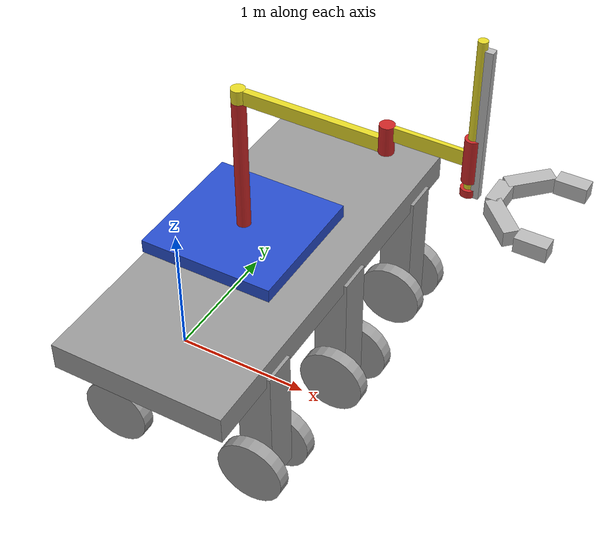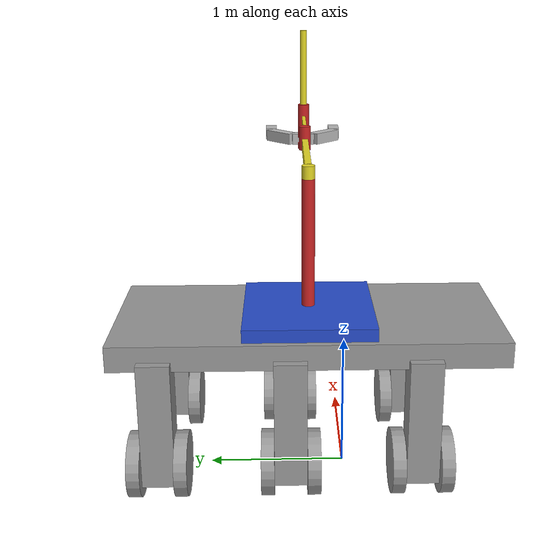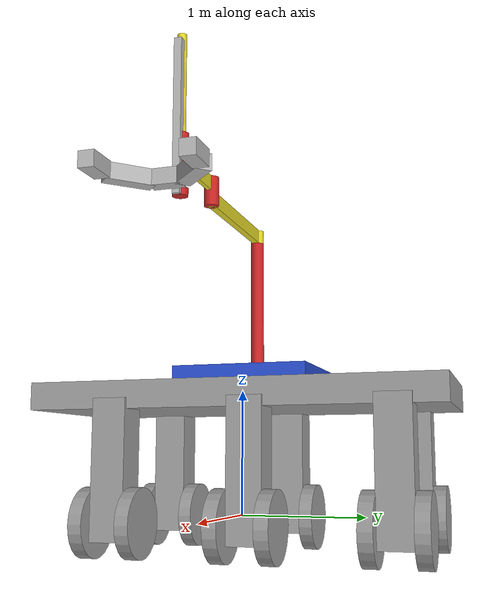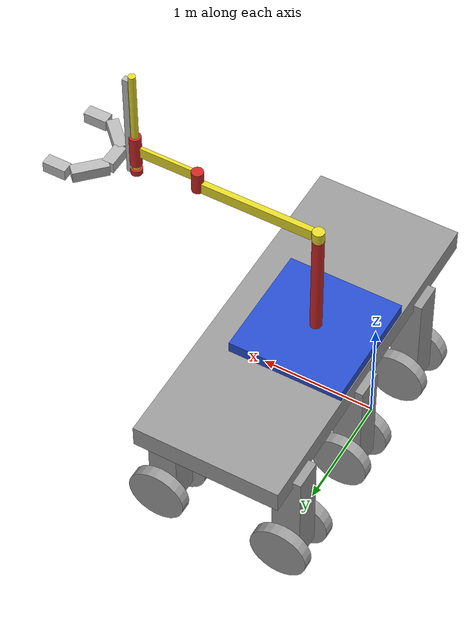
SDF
<?xml version='1.0'?>
<sdf version='1.6'>
  <model name='IanRobot2'>
    <link name='link_0'>
      <inertial>
        <mass>0.104117</mass>
        <inertia>
          <ixx>0.00921869</ixx>
          <ixy>0</ixy>
          <ixz>0</ixz>
          <iyy>0.00921869</iyy>
          <iyz>0</iyz>
          <izz>0.00108455</izz>
        </inertia>
        <pose frame=''>0 0 0.25 0 -0 0</pose>
      </inertial>
      <pose frame=''>0.084444 -0.605838 -0 0 -0 0</pose>
      <gravity>1</gravity>
      <self_collide>0</self_collide>
      <kinematic>0</kinematic>
      <enable_wind>0</enable_wind>
      <visual name='visual'>
        <pose frame=''>-0.125 0 0.375 0 -0 0</pose>
        <geometry>
          <box>
            <size>0.25 0.25 1</size>
          </box>
        </geometry>
        <material>
          <lighting>1</lighting>
          <script>
            <uri>file://media/materials/scripts/gazebo.material</uri>
            <name>Gazebo/Grey</name>
          </script>
          <shader type='pixel'>
            <normal_map>__default__</normal_map>
          </shader>
          <ambient>0.3 0.3 0.3 1</ambient>
          <diffuse>0.7 0.7 0.7 1</diffuse>
          <specular>0.01 0.01 0.01 1</specular>
          <emissive>0 0 0 1</emissive>
        </material>
        <transparency>0</transparency>
        <cast_shadows>1</cast_shadows>
      </visual>
      <collision name='collision'>
        <laser_retro>0</laser_retro>
        <max_contacts>10</max_contacts>
        <pose frame=''>-0.125 0 0.375 0 -0 0</pose>
        <geometry>
          <box>
            <size>0.25 0.25 1</size>
          </box>
        </geometry>
        <surface>
          <friction>
            <ode>
              <mu>1</mu>
              <mu2>1</mu2>
              <fdir1>0 0 0</fdir1>
              <slip1>0</slip1>
              <slip2>0</slip2>
            </ode>
            <torsional>
              <coefficient>1</coefficient>
              <patch_radius>0</patch_radius>
              <surface_radius>0</surface_radius>
              <use_patch_radius>1</use_patch_radius>
              <ode>
                <slip>0</slip>
              </ode>
            </torsional>
          </friction>
          <bounce>
            <restitution_coefficient>0</restitution_coefficient>
            <threshold>1e+06</threshold>
          </bounce>
          <contact>
            <collide_without_contact>0</collide_without_contact>
            <collide_without_contact_bitmask>1</collide_without_contact_bitmask>
            <collide_bitmask>1</collide_bitmask>
            <ode>
              <soft_cfm>0</soft_cfm>
              <soft_erp>0.2</soft_erp>
              <kp>1e+13</kp>
              <kd>1</kd>
              <max_vel>0.01</max_vel>
              <min_depth>0</min_depth>
            </ode>
            <bullet>
              <split_impulse>1</split_impulse>
              <split_impulse_penetration_threshold>-0.01</split_impulse_penetration_threshold>
              <soft_cfm>0</soft_cfm>
              <soft_erp>0.2</soft_erp>
              <kp>1e+13</kp>
              <kd>1</kd>
            </bullet>
          </contact>
        </surface>
      </collision>
    </link>
    <link name='link_0_0'>
      <inertial>
        <mass>0.0762942</mass>
        <inertia>
          <ixx>0.057475</ixx>
          <ixy>0</ixy>
          <ixz>0</ixz>
          <iyy>0.0105343</iyy>
          <iyz>0</iyz>
          <izz>0.0675006</izz>
        </inertia>
        <pose frame=''>0 0 0 0 -0 0</pose>
      </inertial>
      <pose frame=''>0.54 0.25 0.9 0 -0 0</pose>
      <gravity>1</gravity>
      <self_collide>0</self_collide>
      <kinematic>0</kinematic>
      <enable_wind>0</enable_wind>
      <visual name='visual'>
        <pose frame=''>0 0 0 0 -0 0</pose>
        <geometry>
          <box>
            <size>1.27157 3 0.2</size>
          </box>
        </geometry>
        <material>
          <lighting>1</lighting>
          <script>
            <uri>file://media/materials/scripts/gazebo.material</uri>
            <name>Gazebo/Grey</name>
          </script>
          <shader type='pixel'>
            <normal_map>__default__</normal_map>
          </shader>
          <ambient>0.3 0.3 0.3 1</ambient>
          <diffuse>0.7 0.7 0.7 1</diffuse>
          <specular>0.01 0.01 0.01 1</specular>
          <emissive>0 0 0 1</emissive>
        </material>
        <transparency>0</transparency>
        <cast_shadows>1</cast_shadows>
      </visual>
      <collision name='collision'>
        <laser_retro>0</laser_retro>
        <max_contacts>10</max_contacts>
        <pose frame=''>0 0 0 0 -0 0</pose>
        <geometry>
          <box>
            <size>1.27157 3 0.2</size>
          </box>
        </geometry>
        <surface>
          <friction>
            <ode>
              <mu>1</mu>
              <mu2>1</mu2>
              <fdir1>0 0 0</fdir1>
              <slip1>0</slip1>
              <slip2>0</slip2>
            </ode>
            <torsional>
              <coefficient>1</coefficient>
              <patch_radius>0</patch_radius>
              <surface_radius>0</surface_radius>
              <use_patch_radius>1</use_patch_radius>
              <ode>
                <slip>0</slip>
              </ode>
            </torsional>
          </friction>
          <bounce>
            <restitution_coefficient>0</restitution_coefficient>
            <threshold>1e+06</threshold>
          </bounce>
          <contact>
            <collide_without_contact>0</collide_without_contact>
            <collide_without_contact_bitmask>1</collide_without_contact_bitmask>
            <collide_bitmask>1</collide_bitmask>
            <ode>
              <soft_cfm>0</soft_cfm>
              <soft_erp>0.2</soft_erp>
              <kp>1e+13</kp>
              <kd>1</kd>
              <max_vel>0.01</max_vel>
              <min_depth>0</min_depth>
            </ode>
            <bullet>
              <split_impulse>1</split_impulse>
              <split_impulse_penetration_threshold>-0.01</split_impulse_penetration_threshold>
              <soft_cfm>0</soft_cfm>
              <soft_erp>0.2</soft_erp>
              <kp>1e+13</kp>
              <kd>1</kd>
            </bullet>
          </contact>
        </surface>
      </collision>
    </link>
    <link name='link_0_clone'>
      <inertial>
        <mass>0.104117</mass>
        <inertia>
          <ixx>0.00965549</ixx>
          <ixy>0</ixy>
          <ixz>0</ixz>
          <iyy>0.00951003</iyy>
          <iyz>0</iyz>
          <izz>0.00181261</izz>
        </inertia>
        <pose frame=''>0 0 0.25 0 -0 0</pose>
      </inertial>
      <pose frame=''>0.084444 0.394159 0 0 -0 0</pose>
      <gravity>1</gravity>
      <self_collide>0</self_collide>
      <kinematic>0</kinematic>
      <enable_wind>0</enable_wind>
      <visual name='visual'>
        <pose frame=''>-0.125 0 0.375 0 -0 0</pose>
        <geometry>
          <box>
            <size>0.25 0.25 1</size>
          </box>
        </geometry>
        <material>
          <lighting>1</lighting>
          <script>
            <uri>file://media/materials/scripts/gazebo.material</uri>
            <name>Gazebo/Grey</name>
          </script>
          <shader type='pixel'>
            <normal_map>__default__</normal_map>
          </shader>
          <ambient>0.3 0.3 0.3 1</ambient>
          <diffuse>0.7 0.7 0.7 1</diffuse>
          <specular>0.01 0.01 0.01 1</specular>
          <emissive>0 0 0 1</emissive>
        </material>
        <transparency>0</transparency>
        <cast_shadows>1</cast_shadows>
      </visual>
      <collision name='collision'>
        <laser_retro>0</laser_retro>
        <max_contacts>10</max_contacts>
        <pose frame=''>-0.125 0 0.375 0 -0 0</pose>
        <geometry>
          <box>
            <size>0.25 0.25 1</size>
          </box>
        </geometry>
        <surface>
          <friction>
            <ode>
              <mu>1</mu>
              <mu2>1</mu2>
              <fdir1>0 0 0</fdir1>
              <slip1>0</slip1>
              <slip2>0</slip2>
            </ode>
            <torsional>
              <coefficient>1</coefficient>
              <patch_radius>0</patch_radius>
              <surface_radius>0</surface_radius>
              <use_patch_radius>1</use_patch_radius>
              <ode>
                <slip>0</slip>
              </ode>
            </torsional>
          </friction>
          <bounce>
            <restitution_coefficient>0</restitution_coefficient>
            <threshold>1e+06</threshold>
          </bounce>
          <contact>
            <collide_without_contact>0</collide_without_contact>
            <collide_without_contact_bitmask>1</collide_without_contact_bitmask>
            <collide_bitmask>1</collide_bitmask>
            <ode>
              <soft_cfm>0</soft_cfm>
              <soft_erp>0.2</soft_erp>
              <kp>1e+13</kp>
              <kd>1</kd>
              <max_vel>0.01</max_vel>
              <min_depth>0</min_depth>
            </ode>
            <bullet>
              <split_impulse>1</split_impulse>
              <split_impulse_penetration_threshold>-0.01</split_impulse_penetration_threshold>
              <soft_cfm>0</soft_cfm>
              <soft_erp>0.2</soft_erp>
              <kp>1e+13</kp>
              <kd>1</kd>
            </bullet>
          </contact>
        </surface>
      </collision>
    </link>
    <link name='link_0_clone_clone'>
      <inertial>
        <mass>0.104117</mass>
        <inertia>
          <ixx>0.00965549</ixx>
          <ixy>0</ixy>
          <ixz>0</ixz>
          <iyy>0.00951003</iyy>
          <iyz>0</iyz>
          <izz>0.00181261</izz>
        </inertia>
        <pose frame=''>0 0 0.25 0 -0 0</pose>
      </inertial>
      <pose frame=''>0.084444 1.39416 0 0 -0 0</pose>
      <gravity>1</gravity>
      <self_collide>0</self_collide>
      <kinematic>0</kinematic>
      <enable_wind>0</enable_wind>
      <visual name='visual'>
        <pose frame=''>-0.125 0 0.375 0 -0 0</pose>
        <geometry>
          <box>
            <size>0.25 0.25 1</size>
          </box>
        </geometry>
        <material>
          <lighting>1</lighting>
          <script>
            <uri>file://media/materials/scripts/gazebo.material</uri>
            <name>Gazebo/Grey</name>
          </script>
          <shader type='pixel'>
            <normal_map>__default__</normal_map>
          </shader>
          <ambient>0.3 0.3 0.3 1</ambient>
          <diffuse>0.7 0.7 0.7 1</diffuse>
          <specular>0.01 0.01 0.01 1</specular>
          <emissive>0 0 0 1</emissive>
        </material>
        <transparency>0</transparency>
        <cast_shadows>1</cast_shadows>
      </visual>
      <collision name='collision'>
        <laser_retro>0</laser_retro>
        <max_contacts>10</max_contacts>
        <pose frame=''>-0.125 0 0.375 0 -0 0</pose>
        <geometry>
          <box>
            <size>0.25 0.25 1</size>
          </box>
        </geometry>
        <surface>
          <friction>
            <ode>
              <mu>1</mu>
              <mu2>1</mu2>
              <fdir1>0 0 0</fdir1>
              <slip1>0</slip1>
              <slip2>0</slip2>
            </ode>
            <torsional>
              <coefficient>1</coefficient>
              <patch_radius>0</patch_radius>
              <surface_radius>0</surface_radius>
              <use_patch_radius>1</use_patch_radius>
              <ode>
                <slip>0</slip>
              </ode>
            </torsional>
          </friction>
          <bounce>
            <restitution_coefficient>0</restitution_coefficient>
            <threshold>1e+06</threshold>
          </bounce>
          <contact>
            <collide_without_contact>0</collide_without_contact>
            <collide_without_contact_bitmask>1</collide_without_contact_bitmask>
            <collide_bitmask>1</collide_bitmask>
            <ode>
              <soft_cfm>0</soft_cfm>
              <soft_erp>0.2</soft_erp>
              <kp>1e+13</kp>
              <kd>1</kd>
              <max_vel>0.01</max_vel>
              <min_depth>0</min_depth>
            </ode>
            <bullet>
              <split_impulse>1</split_impulse>
              <split_impulse_penetration_threshold>-0.01</split_impulse_penetration_threshold>
              <soft_cfm>0</soft_cfm>
              <soft_erp>0.2</soft_erp>
              <kp>1e+13</kp>
              <kd>1</kd>
            </bullet>
          </contact>
        </surface>
      </collision>
    </link>
    <link name='link_0_clone_clone_clone'>
      <inertial>
        <mass>0.104117</mass>
        <inertia>
          <ixx>0.00965549</ixx>
          <ixy>0</ixy>
          <ixz>0</ixz>
          <iyy>0.00951003</iyy>
          <iyz>0</iyz>
          <izz>0.00181261</izz>
        </inertia>
        <pose frame=''>0 0 0.25 0 -0 0</pose>
      </inertial>
      <pose frame=''>1.2 1.39146 0 0 -0 0</pose>
      <gravity>1</gravity>
      <self_collide>0</self_collide>
      <kinematic>0</kinematic>
      <enable_wind>0</enable_wind>
      <visual name='visual'>
        <pose frame=''>-0.125 0 0.375 0 -0 0</pose>
        <geometry>
          <box>
            <size>0.25 0.25 1</size>
          </box>
        </geometry>
        <material>
          <lighting>1</lighting>
          <script>
            <uri>file://media/materials/scripts/gazebo.material</uri>
            <name>Gazebo/Grey</name>
          </script>
          <shader type='pixel'>
            <normal_map>__default__</normal_map>
          </shader>
          <ambient>0.3 0.3 0.3 1</ambient>
          <diffuse>0.7 0.7 0.7 1</diffuse>
          <specular>0.01 0.01 0.01 1</specular>
          <emissive>0 0 0 1</emissive>
        </material>
        <transparency>0</transparency>
        <cast_shadows>1</cast_shadows>
      </visual>
      <collision name='collision'>
        <laser_retro>0</laser_retro>
        <max_contacts>10</max_contacts>
        <pose frame=''>-0.125 0 0.375 0 -0 0</pose>
        <geometry>
          <box>
            <size>0.25 0.25 1</size>
          </box>
        </geometry>
        <surface>
          <friction>
            <ode>
              <mu>1</mu>
              <mu2>1</mu2>
              <fdir1>0 0 0</fdir1>
              <slip1>0</slip1>
              <slip2>0</slip2>
            </ode>
            <torsional>
              <coefficient>1</coefficient>
              <patch_radius>0</patch_radius>
              <surface_radius>0</surface_radius>
              <use_patch_radius>1</use_patch_radius>
              <ode>
                <slip>0</slip>
              </ode>
            </torsional>
          </friction>
          <bounce>
            <restitution_coefficient>0</restitution_coefficient>
            <threshold>1e+06</threshold>
          </bounce>
          <contact>
            <collide_without_contact>0</collide_without_contact>
            <collide_without_contact_bitmask>1</collide_without_contact_bitmask>
            <collide_bitmask>1</collide_bitmask>
            <ode>
              <soft_cfm>0</soft_cfm>
              <soft_erp>0.2</soft_erp>
              <kp>1e+13</kp>
              <kd>1</kd>
              <max_vel>0.01</max_vel>
              <min_depth>0</min_depth>
            </ode>
            <bullet>
              <split_impulse>1</split_impulse>
              <split_impulse_penetration_threshold>-0.01</split_impulse_penetration_threshold>
              <soft_cfm>0</soft_cfm>
              <soft_erp>0.2</soft_erp>
              <kp>1e+13</kp>
              <kd>1</kd>
            </bullet>
          </contact>
        </surface>
      </collision>
    </link>
    <link name='link_0_clone_clone_clone_clone'>
      <inertial>
        <mass>0.104117</mass>
        <inertia>
          <ixx>0.00965549</ixx>
          <ixy>0</ixy>
          <ixz>0</ixz>
          <iyy>0.00951003</iyy>
          <iyz>0</iyz>
          <izz>0.00181261</izz>
        </inertia>
        <pose frame=''>0 0 0.25 0 -0 0</pose>
      </inertial>
      <pose frame=''>1.2 0.394159 0 0 -0 0</pose>
      <gravity>1</gravity>
      <self_collide>0</self_collide>
      <kinematic>0</kinematic>
      <enable_wind>0</enable_wind>
      <visual name='visual'>
        <pose frame=''>-0.125 0 0.375 0 -0 0</pose>
        <geometry>
          <box>
            <size>0.25 0.25 1</size>
          </box>
        </geometry>
        <material>
          <lighting>1</lighting>
          <script>
            <uri>file://media/materials/scripts/gazebo.material</uri>
            <name>Gazebo/Grey</name>
          </script>
          <shader type='pixel'>
            <normal_map>__default__</normal_map>
          </shader>
          <ambient>0.3 0.3 0.3 1</ambient>
          <diffuse>0.7 0.7 0.7 1</diffuse>
          <specular>0.01 0.01 0.01 1</specular>
          <emissive>0 0 0 1</emissive>
        </material>
        <transparency>0</transparency>
        <cast_shadows>1</cast_shadows>
      </visual>
      <collision name='collision'>
        <laser_retro>0</laser_retro>
        <max_contacts>10</max_contacts>
        <pose frame=''>-0.125 0 0.375 0 -0 0</pose>
        <geometry>
          <box>
            <size>0.25 0.25 1</size>
          </box>
        </geometry>
        <surface>
          <friction>
            <ode>
              <mu>1</mu>
              <mu2>1</mu2>
              <fdir1>0 0 0</fdir1>
              <slip1>0</slip1>
              <slip2>0</slip2>
            </ode>
            <torsional>
              <coefficient>1</coefficient>
              <patch_radius>0</patch_radius>
              <surface_radius>0</surface_radius>
              <use_patch_radius>1</use_patch_radius>
              <ode>
                <slip>0</slip>
              </ode>
            </torsional>
          </friction>
          <bounce>
            <restitution_coefficient>0</restitution_coefficient>
            <threshold>1e+06</threshold>
          </bounce>
          <contact>
            <collide_without_contact>0</collide_without_contact>
            <collide_without_contact_bitmask>1</collide_without_contact_bitmask>
            <collide_bitmask>1</collide_bitmask>
            <ode>
              <soft_cfm>0</soft_cfm>
              <soft_erp>0.2</soft_erp>
              <kp>1e+13</kp>
              <kd>1</kd>
              <max_vel>0.01</max_vel>
              <min_depth>0</min_depth>
            </ode>
            <bullet>
              <split_impulse>1</split_impulse>
              <split_impulse_penetration_threshold>-0.01</split_impulse_penetration_threshold>
              <soft_cfm>0</soft_cfm>
              <soft_erp>0.2</soft_erp>
              <kp>1e+13</kp>
              <kd>1</kd>
            </bullet>
          </contact>
        </surface>
      </collision>
    </link>
    <link name='link_0_clone_clone_clone_clone_clone'>
      <inertial>
        <mass>0.104117</mass>
        <inertia>
          <ixx>0.00965549</ixx>
          <ixy>0</ixy>
          <ixz>0</ixz>
          <iyy>0.00951003</iyy>
          <iyz>0</iyz>
          <izz>0.00181261</izz>
        </inertia>
        <pose frame=''>0 0 0.25 0 -0 0</pose>
      </inertial>
      <pose frame=''>1.2 -0.605838 0 0 -0 0</pose>
      <gravity>1</gravity>
      <self_collide>0</self_collide>
      <kinematic>0</kinematic>
      <enable_wind>0</enable_wind>
      <visual name='visual'>
        <pose frame=''>-0.125 0 0.375 0 -0 0</pose>
        <geometry>
          <box>
            <size>0.25 0.25 1</size>
          </box>
        </geometry>
        <material>
          <lighting>1</lighting>
          <script>
            <uri>file://media/materials/scripts/gazebo.material</uri>
            <name>Gazebo/Grey</name>
          </script>
          <shader type='pixel'>
            <normal_map>__default__</normal_map>
          </shader>
          <ambient>0.3 0.3 0.3 1</ambient>
          <diffuse>0.7 0.7 0.7 1</diffuse>
          <specular>0.01 0.01 0.01 1</specular>
          <emissive>0 0 0 1</emissive>
        </material>
        <transparency>0</transparency>
        <cast_shadows>1</cast_shadows>
      </visual>
      <collision name='collision'>
        <laser_retro>0</laser_retro>
        <max_contacts>10</max_contacts>
        <pose frame=''>-0.125 0 0.375 0 -0 0</pose>
        <geometry>
          <box>
            <size>0.25 0.25 1</size>
          </box>
        </geometry>
        <surface>
          <friction>
            <ode>
              <mu>1</mu>
              <mu2>1</mu2>
              <fdir1>0 0 0</fdir1>
              <slip1>0</slip1>
              <slip2>0</slip2>
            </ode>
            <torsional>
              <coefficient>1</coefficient>
              <patch_radius>0</patch_radius>
              <surface_radius>0</surface_radius>
              <use_patch_radius>1</use_patch_radius>
              <ode>
                <slip>0</slip>
              </ode>
            </torsional>
          </friction>
          <bounce>
            <restitution_coefficient>0</restitution_coefficient>
            <threshold>1e+06</threshold>
          </bounce>
          <contact>
            <collide_without_contact>0</collide_without_contact>
            <collide_without_contact_bitmask>1</collide_without_contact_bitmask>
            <collide_bitmask>1</collide_bitmask>
            <ode>
              <soft_cfm>0</soft_cfm>
              <soft_erp>0.2</soft_erp>
              <kp>1e+13</kp>
              <kd>1</kd>
              <max_vel>0.01</max_vel>
              <min_depth>0</min_depth>
            </ode>
            <bullet>
              <split_impulse>1</split_impulse>
              <split_impulse_penetration_threshold>-0.01</split_impulse_penetration_threshold>
              <soft_cfm>0</soft_cfm>
              <soft_erp>0.2</soft_erp>
              <kp>1e+13</kp>
              <kd>1</kd>
            </bullet>
          </contact>
        </surface>
      </collision>
    </link>
    <link name='link_1'>
      <inertial>
        <mass>1</mass>
        <inertia>
          <ixx>0.145833</ixx>
          <ixy>0</ixy>
          <ixz>0</ixz>
          <iyy>0.145833</iyy>
          <iyz>0</iyz>
          <izz>0.125</izz>
        </inertia>
        <pose frame=''>0 0 0 0 -0 0</pose>
      </inertial>
      <pose frame=''>-0.025555 -0.415864 0 1.5707 -0 0</pose>
      <gravity>1</gravity>
      <self_collide>0</self_collide>
      <kinematic>0</kinematic>
      <enable_wind>0</enable_wind>
      <visual name='visual'>
        <pose frame=''>0 0 0 0 -0 0</pose>
        <geometry>
          <cylinder>
            <radius>0.25</radius>
            <length>0.1</length>
          </cylinder>
        </geometry>
        <material>
          <lighting>1</lighting>
          <script>
            <uri>file://media/materials/scripts/gazebo.material</uri>
            <name>Gazebo/Grey</name>
          </script>
          <shader type='pixel'>
            <normal_map>__default__</normal_map>
          </shader>
          <ambient>0.3 0.3 0.3 1</ambient>
          <diffuse>0.7 0.7 0.7 1</diffuse>
          <specular>0.01 0.01 0.01 1</specular>
          <emissive>0 0 0 1</emissive>
        </material>
        <transparency>0</transparency>
        <cast_shadows>1</cast_shadows>
      </visual>
      <collision name='collision'>
        <laser_retro>0</laser_retro>
        <max_contacts>10</max_contacts>
        <pose frame=''>0 0 0 0 -0 0</pose>
        <geometry>
          <cylinder>
            <radius>0.25</radius>
            <length>0.1</length>
          </cylinder>
        </geometry>
        <surface>
          <friction>
            <ode>
              <mu>1</mu>
              <mu2>1</mu2>
              <fdir1>0 0 0</fdir1>
              <slip1>0</slip1>
              <slip2>0</slip2>
            </ode>
            <torsional>
              <coefficient>1</coefficient>
              <patch_radius>0</patch_radius>
              <surface_radius>0</surface_radius>
              <use_patch_radius>1</use_patch_radius>
              <ode>
                <slip>0</slip>
              </ode>
            </torsional>
          </friction>
          <bounce>
            <restitution_coefficient>0</restitution_coefficient>
            <threshold>1e+06</threshold>
          </bounce>
          <contact>
            <collide_without_contact>0</collide_without_contact>
            <collide_without_contact_bitmask>1</collide_without_contact_bitmask>
            <collide_bitmask>1</collide_bitmask>
            <ode>
              <soft_cfm>0</soft_cfm>
              <soft_erp>0.2</soft_erp>
              <kp>1e+13</kp>
              <kd>1</kd>
              <max_vel>0.01</max_vel>
              <min_depth>0</min_depth>
            </ode>
            <bullet>
              <split_impulse>1</split_impulse>
              <split_impulse_penetration_threshold>-0.01</split_impulse_penetration_threshold>
              <soft_cfm>0</soft_cfm>
              <soft_erp>0.2</soft_erp>
              <kp>1e+13</kp>
              <kd>1</kd>
            </bullet>
          </contact>
        </surface>
      </collision>
    </link>
    <link name='link_1_clone'>
      <inertial>
        <mass>1</mass>
        <inertia>
          <ixx>0.145833</ixx>
          <ixy>0</ixy>
          <ixz>0</ixz>
          <iyy>0.145833</iyy>
          <iyz>0</iyz>
          <izz>0.125</izz>
        </inertia>
        <pose frame=''>0 0 0 0 -0 0</pose>
      </inertial>
      <pose frame=''>-0.025555 -0.780864 0 1.5707 -0 0</pose>
      <gravity>1</gravity>
      <self_collide>0</self_collide>
      <kinematic>0</kinematic>
      <enable_wind>0</enable_wind>
      <visual name='visual'>
        <pose frame=''>0 0 0 0 -0 0</pose>
        <geometry>
          <cylinder>
            <radius>0.25</radius>
            <length>0.1</length>
          </cylinder>
        </geometry>
        <material>
          <lighting>1</lighting>
          <script>
            <uri>file://media/materials/scripts/gazebo.material</uri>
            <name>Gazebo/Grey</name>
          </script>
          <shader type='pixel'>
            <normal_map>__default__</normal_map>
          </shader>
          <ambient>0.3 0.3 0.3 1</ambient>
          <diffuse>0.7 0.7 0.7 1</diffuse>
          <specular>0.01 0.01 0.01 1</specular>
          <emissive>0 0 0 1</emissive>
        </material>
        <transparency>0</transparency>
        <cast_shadows>1</cast_shadows>
      </visual>
      <collision name='collision'>
        <laser_retro>0</laser_retro>
        <max_contacts>10</max_contacts>
        <pose frame=''>0 0 0 0 -0 0</pose>
        <geometry>
          <cylinder>
            <radius>0.25</radius>
            <length>0.1</length>
          </cylinder>
        </geometry>
        <surface>
          <friction>
            <ode>
              <mu>1</mu>
              <mu2>1</mu2>
              <fdir1>0 0 0</fdir1>
              <slip1>0</slip1>
              <slip2>0</slip2>
            </ode>
            <torsional>
              <coefficient>1</coefficient>
              <patch_radius>0</patch_radius>
              <surface_radius>0</surface_radius>
              <use_patch_radius>1</use_patch_radius>
              <ode>
                <slip>0</slip>
              </ode>
            </torsional>
          </friction>
          <bounce>
            <restitution_coefficient>0</restitution_coefficient>
            <threshold>1e+06</threshold>
          </bounce>
          <contact>
            <collide_without_contact>0</collide_without_contact>
            <collide_without_contact_bitmask>1</collide_without_contact_bitmask>
            <collide_bitmask>1</collide_bitmask>
            <ode>
              <soft_cfm>0</soft_cfm>
              <soft_erp>0.2</soft_erp>
              <kp>1e+13</kp>
              <kd>1</kd>
              <max_vel>0.01</max_vel>
              <min_depth>0</min_depth>
            </ode>
            <bullet>
              <split_impulse>1</split_impulse>
              <split_impulse_penetration_threshold>-0.01</split_impulse_penetration_threshold>
              <soft_cfm>0</soft_cfm>
              <soft_erp>0.2</soft_erp>
              <kp>1e+13</kp>
              <kd>1</kd>
            </bullet>
          </contact>
        </surface>
      </collision>
    </link>
    <link name='link_1_clone_0'>
      <inertial>
        <mass>1</mass>
        <inertia>
          <ixx>0.145833</ixx>
          <ixy>0</ixy>
          <ixz>0</ixz>
          <iyy>0.145833</iyy>
          <iyz>0</iyz>
          <izz>0.125</izz>
        </inertia>
        <pose frame=''>0 0 0 0 -0 0</pose>
      </inertial>
      <pose frame=''>-0.025555 0.569183 0 1.5707 -0 0</pose>
      <gravity>1</gravity>
      <self_collide>0</self_collide>
      <kinematic>0</kinematic>
      <enable_wind>0</enable_wind>
      <visual name='visual'>
        <pose frame=''>0 0 0 0 -0 0</pose>
        <geometry>
          <cylinder>
            <radius>0.25</radius>
            <length>0.1</length>
          </cylinder>
        </geometry>
        <material>
          <lighting>1</lighting>
          <script>
            <uri>file://media/materials/scripts/gazebo.material</uri>
            <name>Gazebo/Grey</name>
          </script>
          <shader type='pixel'>
            <normal_map>__default__</normal_map>
          </shader>
          <ambient>0.3 0.3 0.3 1</ambient>
          <diffuse>0.7 0.7 0.7 1</diffuse>
          <specular>0.01 0.01 0.01 1</specular>
          <emissive>0 0 0 1</emissive>
        </material>
        <transparency>0</transparency>
        <cast_shadows>1</cast_shadows>
      </visual>
      <collision name='collision'>
        <laser_retro>0</laser_retro>
        <max_contacts>10</max_contacts>
        <pose frame=''>0 0 0 0 -0 0</pose>
        <geometry>
          <cylinder>
            <radius>0.25</radius>
            <length>0.1</length>
          </cylinder>
        </geometry>
        <surface>
          <friction>
            <ode>
              <mu>1</mu>
              <mu2>1</mu2>
              <fdir1>0 0 0</fdir1>
              <slip1>0</slip1>
              <slip2>0</slip2>
            </ode>
            <torsional>
              <coefficient>1</coefficient>
              <patch_radius>0</patch_radius>
              <surface_radius>0</surface_radius>
              <use_patch_radius>1</use_patch_radius>
              <ode>
                <slip>0</slip>
              </ode>
            </torsional>
          </friction>
          <bounce>
            <restitution_coefficient>0</restitution_coefficient>
            <threshold>1e+06</threshold>
          </bounce>
          <contact>
            <collide_without_contact>0</collide_without_contact>
            <collide_without_contact_bitmask>1</collide_without_contact_bitmask>
            <collide_bitmask>1</collide_bitmask>
            <ode>
              <soft_cfm>0</soft_cfm>
              <soft_erp>0.2</soft_erp>
              <kp>1e+13</kp>
              <kd>1</kd>
              <max_vel>0.01</max_vel>
              <min_depth>0</min_depth>
            </ode>
            <bullet>
              <split_impulse>1</split_impulse>
              <split_impulse_penetration_threshold>-0.01</split_impulse_penetration_threshold>
              <soft_cfm>0</soft_cfm>
              <soft_erp>0.2</soft_erp>
              <kp>1e+13</kp>
              <kd>1</kd>
            </bullet>
          </contact>
        </surface>
      </collision>
    </link>
    <link name='link_1_clone_1'>
      <inertial>
        <mass>1</mass>
        <inertia>
          <ixx>0.145833</ixx>
          <ixy>0</ixy>
          <ixz>0</ixz>
          <iyy>0.145833</iyy>
          <iyz>0</iyz>
          <izz>0.125</izz>
        </inertia>
        <pose frame=''>0 0 0 0 -0 0</pose>
      </inertial>
      <pose frame=''>-0.025555 0.219135 0 1.5707 -0 0</pose>
      <gravity>1</gravity>
      <self_collide>0</self_collide>
      <kinematic>0</kinematic>
      <enable_wind>0</enable_wind>
      <visual name='visual'>
        <pose frame=''>0 0 0 0 -0 0</pose>
        <geometry>
          <cylinder>
            <radius>0.25</radius>
            <length>0.1</length>
          </cylinder>
        </geometry>
        <material>
          <lighting>1</lighting>
          <script>
            <uri>file://media/materials/scripts/gazebo.material</uri>
            <name>Gazebo/Grey</name>
          </script>
          <shader type='pixel'>
            <normal_map>__default__</normal_map>
          </shader>
          <ambient>0.3 0.3 0.3 1</ambient>
          <diffuse>0.7 0.7 0.7 1</diffuse>
          <specular>0.01 0.01 0.01 1</specular>
          <emissive>0 0 0 1</emissive>
        </material>
        <transparency>0</transparency>
        <cast_shadows>1</cast_shadows>
      </visual>
      <collision name='collision'>
        <laser_retro>0</laser_retro>
        <max_contacts>10</max_contacts>
        <pose frame=''>0 0 0 0 -0 0</pose>
        <geometry>
          <cylinder>
            <radius>0.25</radius>
            <length>0.1</length>
          </cylinder>
        </geometry>
        <surface>
          <friction>
            <ode>
              <mu>1</mu>
              <mu2>1</mu2>
              <fdir1>0 0 0</fdir1>
              <slip1>0</slip1>
              <slip2>0</slip2>
            </ode>
            <torsional>
              <coefficient>1</coefficient>
              <patch_radius>0</patch_radius>
              <surface_radius>0</surface_radius>
              <use_patch_radius>1</use_patch_radius>
              <ode>
                <slip>0</slip>
              </ode>
            </torsional>
          </friction>
          <bounce>
            <restitution_coefficient>0</restitution_coefficient>
            <threshold>1e+06</threshold>
          </bounce>
          <contact>
            <collide_without_contact>0</collide_without_contact>
            <collide_without_contact_bitmask>1</collide_without_contact_bitmask>
            <collide_bitmask>1</collide_bitmask>
            <ode>
              <soft_cfm>0</soft_cfm>
              <soft_erp>0.2</soft_erp>
              <kp>1e+13</kp>
              <kd>1</kd>
              <max_vel>0.01</max_vel>
              <min_depth>0</min_depth>
            </ode>
            <bullet>
              <split_impulse>1</split_impulse>
              <split_impulse_penetration_threshold>-0.01</split_impulse_penetration_threshold>
              <soft_cfm>0</soft_cfm>
              <soft_erp>0.2</soft_erp>
              <kp>1e+13</kp>
              <kd>1</kd>
            </bullet>
          </contact>
        </surface>
      </collision>
    </link>
    <link name='link_1_clone_1_clone'>
      <inertial>
        <mass>1</mass>
        <inertia>
          <ixx>0.145833</ixx>
          <ixy>0</ixy>
          <ixz>0</ixz>
          <iyy>0.145833</iyy>
          <iyz>0</iyz>
          <izz>0.125</izz>
        </inertia>
        <pose frame=''>0 0 0 0 -0 0</pose>
      </inertial>
      <pose frame=''>-0.025555 1.21914 0 1.5707 -0 0</pose>
      <gravity>1</gravity>
      <self_collide>0</self_collide>
      <kinematic>0</kinematic>
      <enable_wind>0</enable_wind>
      <visual name='visual'>
        <pose frame=''>0 0 0 0 -0 0</pose>
        <geometry>
          <cylinder>
            <radius>0.25</radius>
            <length>0.1</length>
          </cylinder>
        </geometry>
        <material>
          <lighting>1</lighting>
          <script>
            <uri>file://media/materials/scripts/gazebo.material</uri>
            <name>Gazebo/Grey</name>
          </script>
          <shader type='pixel'>
            <normal_map>__default__</normal_map>
          </shader>
          <ambient>0.3 0.3 0.3 1</ambient>
          <diffuse>0.7 0.7 0.7 1</diffuse>
          <specular>0.01 0.01 0.01 1</specular>
          <emissive>0 0 0 1</emissive>
        </material>
        <transparency>0</transparency>
        <cast_shadows>1</cast_shadows>
      </visual>
      <collision name='collision'>
        <laser_retro>0</laser_retro>
        <max_contacts>10</max_contacts>
        <pose frame=''>0 0 0 0 -0 0</pose>
        <geometry>
          <cylinder>
            <radius>0.25</radius>
            <length>0.1</length>
          </cylinder>
        </geometry>
        <surface>
          <friction>
            <ode>
              <mu>1</mu>
              <mu2>1</mu2>
              <fdir1>0 0 0</fdir1>
              <slip1>0</slip1>
              <slip2>0</slip2>
            </ode>
            <torsional>
              <coefficient>1</coefficient>
              <patch_radius>0</patch_radius>
              <surface_radius>0</surface_radius>
              <use_patch_radius>1</use_patch_radius>
              <ode>
                <slip>0</slip>
              </ode>
            </torsional>
          </friction>
          <bounce>
            <restitution_coefficient>0</restitution_coefficient>
            <threshold>1e+06</threshold>
          </bounce>
          <contact>
            <collide_without_contact>0</collide_without_contact>
            <collide_without_contact_bitmask>1</collide_without_contact_bitmask>
            <collide_bitmask>1</collide_bitmask>
            <ode>
              <soft_cfm>0</soft_cfm>
              <soft_erp>0.2</soft_erp>
              <kp>1e+13</kp>
              <kd>1</kd>
              <max_vel>0.01</max_vel>
              <min_depth>0</min_depth>
            </ode>
            <bullet>
              <split_impulse>1</split_impulse>
              <split_impulse_penetration_threshold>-0.01</split_impulse_penetration_threshold>
              <soft_cfm>0</soft_cfm>
              <soft_erp>0.2</soft_erp>
              <kp>1e+13</kp>
              <kd>1</kd>
            </bullet>
          </contact>
        </surface>
      </collision>
    </link>
    <link name='link_1_clone_1_clone_clone'>
      <inertial>
        <mass>1</mass>
        <inertia>
          <ixx>0.145833</ixx>
          <ixy>0</ixy>
          <ixz>0</ixz>
          <iyy>0.145833</iyy>
          <iyz>0</iyz>
          <izz>0.125</izz>
        </inertia>
        <pose frame=''>0 0 0 0 -0 0</pose>
      </inertial>
      <pose frame=''>-0.025555 1.56918 0 1.5707 -0 0</pose>
      <gravity>1</gravity>
      <self_collide>0</self_collide>
      <kinematic>0</kinematic>
      <enable_wind>0</enable_wind>
      <visual name='visual'>
        <pose frame=''>0 0 0 0 -0 0</pose>
        <geometry>
          <cylinder>
            <radius>0.25</radius>
            <length>0.1</length>
          </cylinder>
        </geometry>
        <material>
          <lighting>1</lighting>
          <script>
            <uri>file://media/materials/scripts/gazebo.material</uri>
            <name>Gazebo/Grey</name>
          </script>
          <shader type='pixel'>
            <normal_map>__default__</normal_map>
          </shader>
          <ambient>0.3 0.3 0.3 1</ambient>
          <diffuse>0.7 0.7 0.7 1</diffuse>
          <specular>0.01 0.01 0.01 1</specular>
          <emissive>0 0 0 1</emissive>
        </material>
        <transparency>0</transparency>
        <cast_shadows>1</cast_shadows>
      </visual>
      <collision name='collision'>
        <laser_retro>0</laser_retro>
        <max_contacts>10</max_contacts>
        <pose frame=''>0 0 0 0 -0 0</pose>
        <geometry>
          <cylinder>
            <radius>0.25</radius>
            <length>0.1</length>
          </cylinder>
        </geometry>
        <surface>
          <friction>
            <ode>
              <mu>1</mu>
              <mu2>1</mu2>
              <fdir1>0 0 0</fdir1>
              <slip1>0</slip1>
              <slip2>0</slip2>
            </ode>
            <torsional>
              <coefficient>1</coefficient>
              <patch_radius>0</patch_radius>
              <surface_radius>0</surface_radius>
              <use_patch_radius>1</use_patch_radius>
              <ode>
                <slip>0</slip>
              </ode>
            </torsional>
          </friction>
          <bounce>
            <restitution_coefficient>0</restitution_coefficient>
            <threshold>1e+06</threshold>
          </bounce>
          <contact>
            <collide_without_contact>0</collide_without_contact>
            <collide_without_contact_bitmask>1</collide_without_contact_bitmask>
            <collide_bitmask>1</collide_bitmask>
            <ode>
              <soft_cfm>0</soft_cfm>
              <soft_erp>0.2</soft_erp>
              <kp>1e+13</kp>
              <kd>1</kd>
              <max_vel>0.01</max_vel>
              <min_depth>0</min_depth>
            </ode>
            <bullet>
              <split_impulse>1</split_impulse>
              <split_impulse_penetration_threshold>-0.01</split_impulse_penetration_threshold>
              <soft_cfm>0</soft_cfm>
              <soft_erp>0.2</soft_erp>
              <kp>1e+13</kp>
              <kd>1</kd>
            </bullet>
          </contact>
        </surface>
      </collision>
    </link>
    <link name='link_1_clone_1_clone_clone_0'>
      <inertial>
        <mass>1</mass>
        <inertia>
          <ixx>0.145833</ixx>
          <ixy>0</ixy>
          <ixz>0</ixz>
          <iyy>0.145833</iyy>
          <iyz>0</iyz>
          <izz>0.125</izz>
        </inertia>
        <pose frame=''>0 0 0 0 -0 0</pose>
      </inertial>
      <pose frame=''>1.08444 1.21914 0 1.5707 -0 0</pose>
      <gravity>1</gravity>
      <self_collide>0</self_collide>
      <kinematic>0</kinematic>
      <enable_wind>0</enable_wind>
      <visual name='visual'>
        <pose frame=''>0 0 0 0 -0 0</pose>
        <geometry>
          <cylinder>
            <radius>0.25</radius>
            <length>0.1</length>
          </cylinder>
        </geometry>
        <material>
          <lighting>1</lighting>
          <script>
            <uri>file://media/materials/scripts/gazebo.material</uri>
            <name>Gazebo/Grey</name>
          </script>
          <shader type='pixel'>
            <normal_map>__default__</normal_map>
          </shader>
          <ambient>0.3 0.3 0.3 1</ambient>
          <diffuse>0.7 0.7 0.7 1</diffuse>
          <specular>0.01 0.01 0.01 1</specular>
          <emissive>0 0 0 1</emissive>
        </material>
        <transparency>0</transparency>
        <cast_shadows>1</cast_shadows>
      </visual>
      <collision name='collision'>
        <laser_retro>0</laser_retro>
        <max_contacts>10</max_contacts>
        <pose frame=''>0 0 0 0 -0 0</pose>
        <geometry>
          <cylinder>
            <radius>0.25</radius>
            <length>0.1</length>
          </cylinder>
        </geometry>
        <surface>
          <friction>
            <ode>
              <mu>1</mu>
              <mu2>1</mu2>
              <fdir1>0 0 0</fdir1>
              <slip1>0</slip1>
              <slip2>0</slip2>
            </ode>
            <torsional>
              <coefficient>1</coefficient>
              <patch_radius>0</patch_radius>
              <surface_radius>0</surface_radius>
              <use_patch_radius>1</use_patch_radius>
              <ode>
                <slip>0</slip>
              </ode>
            </torsional>
          </friction>
          <bounce>
            <restitution_coefficient>0</restitution_coefficient>
            <threshold>1e+06</threshold>
          </bounce>
          <contact>
            <collide_without_contact>0</collide_without_contact>
            <collide_without_contact_bitmask>1</collide_without_contact_bitmask>
            <collide_bitmask>1</collide_bitmask>
            <ode>
              <soft_cfm>0</soft_cfm>
              <soft_erp>0.2</soft_erp>
              <kp>1e+13</kp>
              <kd>1</kd>
              <max_vel>0.01</max_vel>
              <min_depth>0</min_depth>
            </ode>
            <bullet>
              <split_impulse>1</split_impulse>
              <split_impulse_penetration_threshold>-0.01</split_impulse_penetration_threshold>
              <soft_cfm>0</soft_cfm>
              <soft_erp>0.2</soft_erp>
              <kp>1e+13</kp>
              <kd>1</kd>
            </bullet>
          </contact>
        </surface>
      </collision>
    </link>
    <link name='link_1_clone_1_clone_clone_0_clone'>
      <inertial>
        <mass>1</mass>
        <inertia>
          <ixx>0.145833</ixx>
          <ixy>0</ixy>
          <ixz>0</ixz>
          <iyy>0.145833</iyy>
          <iyz>0</iyz>
          <izz>0.125</izz>
        </inertia>
        <pose frame=''>0 0 0 0 -0 0</pose>
      </inertial>
      <pose frame=''>1.1362 0.219135 0 1.5707 -0 0</pose>
      <gravity>1</gravity>
      <self_collide>0</self_collide>
      <kinematic>0</kinematic>
      <enable_wind>0</enable_wind>
      <visual name='visual'>
        <pose frame=''>0 0 0 0 -0 0</pose>
        <geometry>
          <cylinder>
            <radius>0.25</radius>
            <length>0.1</length>
          </cylinder>
        </geometry>
        <material>
          <lighting>1</lighting>
          <script>
            <uri>file://media/materials/scripts/gazebo.material</uri>
            <name>Gazebo/Grey</name>
          </script>
          <shader type='pixel'>
            <normal_map>__default__</normal_map>
          </shader>
          <ambient>0.3 0.3 0.3 1</ambient>
          <diffuse>0.7 0.7 0.7 1</diffuse>
          <specular>0.01 0.01 0.01 1</specular>
          <emissive>0 0 0 1</emissive>
        </material>
        <transparency>0</transparency>
        <cast_shadows>1</cast_shadows>
      </visual>
      <collision name='collision'>
        <laser_retro>0</laser_retro>
        <max_contacts>10</max_contacts>
        <pose frame=''>0 0 0 0 -0 0</pose>
        <geometry>
          <cylinder>
            <radius>0.25</radius>
            <length>0.1</length>
          </cylinder>
        </geometry>
        <surface>
          <friction>
            <ode>
              <mu>1</mu>
              <mu2>1</mu2>
              <fdir1>0 0 0</fdir1>
              <slip1>0</slip1>
              <slip2>0</slip2>
            </ode>
            <torsional>
              <coefficient>1</coefficient>
              <patch_radius>0</patch_radius>
              <surface_radius>0</surface_radius>
              <use_patch_radius>1</use_patch_radius>
              <ode>
                <slip>0</slip>
              </ode>
            </torsional>
          </friction>
          <bounce>
            <restitution_coefficient>0</restitution_coefficient>
            <threshold>1e+06</threshold>
          </bounce>
          <contact>
            <collide_without_contact>0</collide_without_contact>
            <collide_without_contact_bitmask>1</collide_without_contact_bitmask>
            <collide_bitmask>1</collide_bitmask>
            <ode>
              <soft_cfm>0</soft_cfm>
              <soft_erp>0.2</soft_erp>
              <kp>1e+13</kp>
              <kd>1</kd>
              <max_vel>0.01</max_vel>
              <min_depth>0</min_depth>
            </ode>
            <bullet>
              <split_impulse>1</split_impulse>
              <split_impulse_penetration_threshold>-0.01</split_impulse_penetration_threshold>
              <soft_cfm>0</soft_cfm>
              <soft_erp>0.2</soft_erp>
              <kp>1e+13</kp>
              <kd>1</kd>
            </bullet>
          </contact>
        </surface>
      </collision>
    </link>
    <link name='link_1_clone_1_clone_clone_0_clone_0'>
      <inertial>
        <mass>1</mass>
        <inertia>
          <ixx>0.145833</ixx>
          <ixy>0</ixy>
          <ixz>0</ixz>
          <iyy>0.145833</iyy>
          <iyz>0</iyz>
          <izz>0.125</izz>
        </inertia>
        <pose frame=''>0 0 0 0 -0 0</pose>
      </inertial>
      <pose frame=''>1.14076 0.569183 0 1.5707 -0 0</pose>
      <gravity>1</gravity>
      <self_collide>0</self_collide>
      <kinematic>0</kinematic>
      <enable_wind>0</enable_wind>
      <visual name='visual'>
        <pose frame=''>0 0 0 0 -0 0</pose>
        <geometry>
          <cylinder>
            <radius>0.25</radius>
            <length>0.1</length>
          </cylinder>
        </geometry>
        <material>
          <lighting>1</lighting>
          <script>
            <uri>file://media/materials/scripts/gazebo.material</uri>
            <name>Gazebo/Grey</name>
          </script>
          <shader type='pixel'>
            <normal_map>__default__</normal_map>
          </shader>
          <ambient>0.3 0.3 0.3 1</ambient>
          <diffuse>0.7 0.7 0.7 1</diffuse>
          <specular>0.01 0.01 0.01 1</specular>
          <emissive>0 0 0 1</emissive>
        </material>
        <transparency>0</transparency>
        <cast_shadows>1</cast_shadows>
      </visual>
      <collision name='collision'>
        <laser_retro>0</laser_retro>
        <max_contacts>10</max_contacts>
        <pose frame=''>0 0 0 0 -0 0</pose>
        <geometry>
          <cylinder>
            <radius>0.25</radius>
            <length>0.1</length>
          </cylinder>
        </geometry>
        <surface>
          <friction>
            <ode>
              <mu>1</mu>
              <mu2>1</mu2>
              <fdir1>0 0 0</fdir1>
              <slip1>0</slip1>
              <slip2>0</slip2>
            </ode>
            <torsional>
              <coefficient>1</coefficient>
              <patch_radius>0</patch_radius>
              <surface_radius>0</surface_radius>
              <use_patch_radius>1</use_patch_radius>
              <ode>
                <slip>0</slip>
              </ode>
            </torsional>
          </friction>
          <bounce>
            <restitution_coefficient>0</restitution_coefficient>
            <threshold>1e+06</threshold>
          </bounce>
          <contact>
            <collide_without_contact>0</collide_without_contact>
            <collide_without_contact_bitmask>1</collide_without_contact_bitmask>
            <collide_bitmask>1</collide_bitmask>
            <ode>
              <soft_cfm>0</soft_cfm>
              <soft_erp>0.2</soft_erp>
              <kp>1e+13</kp>
              <kd>1</kd>
              <max_vel>0.01</max_vel>
              <min_depth>0</min_depth>
            </ode>
            <bullet>
              <split_impulse>1</split_impulse>
              <split_impulse_penetration_threshold>-0.01</split_impulse_penetration_threshold>
              <soft_cfm>0</soft_cfm>
              <soft_erp>0.2</soft_erp>
              <kp>1e+13</kp>
              <kd>1</kd>
            </bullet>
          </contact>
        </surface>
      </collision>
    </link>
    <link name='link_1_clone_1_clone_clone_0_clone_clone'>
      <inertial>
        <mass>1</mass>
        <inertia>
          <ixx>0.145833</ixx>
          <ixy>0</ixy>
          <ixz>0</ixz>
          <iyy>0.145833</iyy>
          <iyz>0</iyz>
          <izz>0.125</izz>
        </inertia>
        <pose frame=''>0 0 0 0 -0 0</pose>
      </inertial>
      <pose frame=''>1.075 -0.430814 0 1.5707 -0 0</pose>
      <gravity>1</gravity>
      <self_collide>0</self_collide>
      <kinematic>0</kinematic>
      <enable_wind>0</enable_wind>
      <visual name='visual'>
        <pose frame=''>0 0 0 0 -0 0</pose>
        <geometry>
          <cylinder>
            <radius>0.25</radius>
            <length>0.1</length>
          </cylinder>
        </geometry>
        <material>
          <lighting>1</lighting>
          <script>
            <uri>file://media/materials/scripts/gazebo.material</uri>
            <name>Gazebo/Grey</name>
          </script>
          <shader type='pixel'>
            <normal_map>__default__</normal_map>
          </shader>
          <ambient>0.3 0.3 0.3 1</ambient>
          <diffuse>0.7 0.7 0.7 1</diffuse>
          <specular>0.01 0.01 0.01 1</specular>
          <emissive>0 0 0 1</emissive>
        </material>
        <transparency>0</transparency>
        <cast_shadows>1</cast_shadows>
      </visual>
      <collision name='collision'>
        <laser_retro>0</laser_retro>
        <max_contacts>10</max_contacts>
        <pose frame=''>0 0 0 0 -0 0</pose>
        <geometry>
          <cylinder>
            <radius>0.25</radius>
            <length>0.1</length>
          </cylinder>
        </geometry>
        <surface>
          <friction>
            <ode>
              <mu>1</mu>
              <mu2>1</mu2>
              <fdir1>0 0 0</fdir1>
              <slip1>0</slip1>
              <slip2>0</slip2>
            </ode>
            <torsional>
              <coefficient>1</coefficient>
              <patch_radius>0</patch_radius>
              <surface_radius>0</surface_radius>
              <use_patch_radius>1</use_patch_radius>
              <ode>
                <slip>0</slip>
              </ode>
            </torsional>
          </friction>
          <bounce>
            <restitution_coefficient>0</restitution_coefficient>
            <threshold>1e+06</threshold>
          </bounce>
          <contact>
            <collide_without_contact>0</collide_without_contact>
            <collide_without_contact_bitmask>1</collide_without_contact_bitmask>
            <collide_bitmask>1</collide_bitmask>
            <ode>
              <soft_cfm>0</soft_cfm>
              <soft_erp>0.2</soft_erp>
              <kp>1e+13</kp>
              <kd>1</kd>
              <max_vel>0.01</max_vel>
              <min_depth>0</min_depth>
            </ode>
            <bullet>
              <split_impulse>1</split_impulse>
              <split_impulse_penetration_threshold>-0.01</split_impulse_penetration_threshold>
              <soft_cfm>0</soft_cfm>
              <soft_erp>0.2</soft_erp>
              <kp>1e+13</kp>
              <kd>1</kd>
            </bullet>
          </contact>
        </surface>
      </collision>
    </link>
    <link name='link_1_clone_1_clone_clone_0_clone_clone_0'>
      <inertial>
        <mass>1</mass>
        <inertia>
          <ixx>0.145833</ixx>
          <ixy>0</ixy>
          <ixz>0</ixz>
          <iyy>0.145833</iyy>
          <iyz>0</iyz>
          <izz>0.125</izz>
        </inertia>
        <pose frame=''>0 0 0 0 -0 0</pose>
      </inertial>
      <pose frame=''>1.075 -0.780862 0 1.5707 -0 0</pose>
      <gravity>1</gravity>
      <self_collide>0</self_collide>
      <kinematic>0</kinematic>
      <enable_wind>0</enable_wind>
      <visual name='visual'>
        <pose frame=''>0 0 0 0 -0 0</pose>
        <geometry>
          <cylinder>
            <radius>0.25</radius>
            <length>0.1</length>
          </cylinder>
        </geometry>
        <material>
          <lighting>1</lighting>
          <script>
            <uri>file://media/materials/scripts/gazebo.material</uri>
            <name>Gazebo/Grey</name>
          </script>
          <shader type='pixel'>
            <normal_map>__default__</normal_map>
          </shader>
          <ambient>0.3 0.3 0.3 1</ambient>
          <diffuse>0.7 0.7 0.7 1</diffuse>
          <specular>0.01 0.01 0.01 1</specular>
          <emissive>0 0 0 1</emissive>
        </material>
        <transparency>0</transparency>
        <cast_shadows>1</cast_shadows>
      </visual>
      <collision name='collision'>
        <laser_retro>0</laser_retro>
        <max_contacts>10</max_contacts>
        <pose frame=''>0 0 0 0 -0 0</pose>
        <geometry>
          <cylinder>
            <radius>0.25</radius>
            <length>0.1</length>
          </cylinder>
        </geometry>
        <surface>
          <friction>
            <ode>
              <mu>1</mu>
              <mu2>1</mu2>
              <fdir1>0 0 0</fdir1>
              <slip1>0</slip1>
              <slip2>0</slip2>
            </ode>
            <torsional>
              <coefficient>1</coefficient>
              <patch_radius>0</patch_radius>
              <surface_radius>0</surface_radius>
              <use_patch_radius>1</use_patch_radius>
              <ode>
                <slip>0</slip>
              </ode>
            </torsional>
          </friction>
          <bounce>
            <restitution_coefficient>0</restitution_coefficient>
            <threshold>1e+06</threshold>
          </bounce>
          <contact>
            <collide_without_contact>0</collide_without_contact>
            <collide_without_contact_bitmask>1</collide_without_contact_bitmask>
            <collide_bitmask>1</collide_bitmask>
            <ode>
              <soft_cfm>0</soft_cfm>
              <soft_erp>0.2</soft_erp>
              <kp>1e+13</kp>
              <kd>1</kd>
              <max_vel>0.01</max_vel>
              <min_depth>0</min_depth>
            </ode>
            <bullet>
              <split_impulse>1</split_impulse>
              <split_impulse_penetration_threshold>-0.01</split_impulse_penetration_threshold>
              <soft_cfm>0</soft_cfm>
              <soft_erp>0.2</soft_erp>
              <kp>1e+13</kp>
              <kd>1</kd>
            </bullet>
          </contact>
        </surface>
      </collision>
    </link>
    <link name='link_1_clone_1_clone_clone_clone'>
      <inertial>
        <mass>1</mass>
        <inertia>
          <ixx>0.145833</ixx>
          <ixy>0</ixy>
          <ixz>0</ixz>
          <iyy>0.145833</iyy>
          <iyz>0</iyz>
          <izz>0.125</izz>
        </inertia>
        <pose frame=''>0 0 0 0 -0 0</pose>
      </inertial>
      <pose frame=''>1.08444 1.56918 0 1.5707 -0 0</pose>
      <gravity>1</gravity>
      <self_collide>0</self_collide>
      <kinematic>0</kinematic>
      <enable_wind>0</enable_wind>
      <visual name='visual'>
        <pose frame=''>0 0 0 0 -0 0</pose>
        <geometry>
          <cylinder>
            <radius>0.25</radius>
            <length>0.1</length>
          </cylinder>
        </geometry>
        <material>
          <lighting>1</lighting>
          <script>
            <uri>file://media/materials/scripts/gazebo.material</uri>
            <name>Gazebo/Grey</name>
          </script>
          <shader type='pixel'>
            <normal_map>__default__</normal_map>
          </shader>
          <ambient>0.3 0.3 0.3 1</ambient>
          <diffuse>0.7 0.7 0.7 1</diffuse>
          <specular>0.01 0.01 0.01 1</specular>
          <emissive>0 0 0 1</emissive>
        </material>
        <transparency>0</transparency>
        <cast_shadows>1</cast_shadows>
      </visual>
      <collision name='collision'>
        <laser_retro>0</laser_retro>
        <max_contacts>10</max_contacts>
        <pose frame=''>0 0 0 0 -0 0</pose>
        <geometry>
          <cylinder>
            <radius>0.25</radius>
            <length>0.1</length>
          </cylinder>
        </geometry>
        <surface>
          <friction>
            <ode>
              <mu>1</mu>
              <mu2>1</mu2>
              <fdir1>0 0 0</fdir1>
              <slip1>0</slip1>
              <slip2>0</slip2>
            </ode>
            <torsional>
              <coefficient>1</coefficient>
              <patch_radius>0</patch_radius>
              <surface_radius>0</surface_radius>
              <use_patch_radius>1</use_patch_radius>
              <ode>
                <slip>0</slip>
              </ode>
            </torsional>
          </friction>
          <bounce>
            <restitution_coefficient>0</restitution_coefficient>
            <threshold>1e+06</threshold>
          </bounce>
          <contact>
            <collide_without_contact>0</collide_without_contact>
            <collide_without_contact_bitmask>1</collide_without_contact_bitmask>
            <collide_bitmask>1</collide_bitmask>
            <ode>
              <soft_cfm>0</soft_cfm>
              <soft_erp>0.2</soft_erp>
              <kp>1e+13</kp>
              <kd>1</kd>
              <max_vel>0.01</max_vel>
              <min_depth>0</min_depth>
            </ode>
            <bullet>
              <split_impulse>1</split_impulse>
              <split_impulse_penetration_threshold>-0.01</split_impulse_penetration_threshold>
              <soft_cfm>0</soft_cfm>
              <soft_erp>0.2</soft_erp>
              <kp>1e+13</kp>
              <kd>1</kd>
            </bullet>
          </contact>
        </surface>
      </collision>
    </link>
    <model name='simple_arm_gripper'>
      <link name='simple_arm::arm_base'>
        <inertial>
          <pose frame=''>0 0 0.00099 0 -0 0</pose>
          <inertia>
            <ixx>1.11</ixx>
            <ixy>0</ixy>
            <ixz>0</ixz>
            <iyy>100.11</iyy>
            <iyz>0</iyz>
            <izz>1.01</izz>
          </inertia>
          <mass>101</mass>
        </inertial>
        <collision name='arm_base_geom'>
          <pose frame=''>0 0 0.05 0 -0 0</pose>
          <geometry>
            <box>
              <size>1 1 0.1</size>
            </box>
          </geometry>
          <max_contacts>10</max_contacts>
          <surface>
            <contact>
              <ode/>
            </contact>
            <bounce/>
            <friction>
              <torsional>
                <ode/>
              </torsional>
              <ode/>
            </friction>
          </surface>
        </collision>
        <visual name='arm_base_geom_visual'>
          <pose frame=''>0 0 0.05 0 -0 0</pose>
          <geometry>
            <box>
              <size>1 1 0.1</size>
            </box>
          </geometry>
          <material>
            <script>
              <uri>file://media/materials/scripts/gazebo.material</uri>
              <name>Gazebo/Blue</name>
            </script>
          </material>
        </visual>
        <collision name='arm_base_geom_arm_trunk'>
          <pose frame=''>0 0 0.6 0 -0 0</pose>
          <geometry>
            <cylinder>
              <radius>0.05</radius>
              <length>1</length>
            </cylinder>
          </geometry>
          <max_contacts>10</max_contacts>
          <surface>
            <contact>
              <ode/>
            </contact>
            <bounce/>
            <friction>
              <torsional>
                <ode/>
              </torsional>
              <ode/>
            </friction>
          </surface>
        </collision>
        <visual name='arm_base_geom_arm_trunk_visual'>
          <pose frame=''>0 0 0.6 0 -0 0</pose>
          <geometry>
            <cylinder>
              <radius>0.05</radius>
              <length>1</length>
            </cylinder>
          </geometry>
          <material>
            <script>
              <uri>file://media/materials/scripts/gazebo.material</uri>
              <name>Gazebo/Red</name>
            </script>
          </material>
        </visual>
        <pose frame=''>0 0 0 0 -0 0</pose>
        <self_collide>0</self_collide>
        <enable_wind>0</enable_wind>
        <kinematic>0</kinematic>
      </link>
      <link name='simple_arm::arm_shoulder_pan'>
        <pose frame=''>0 0 1.1 0 -0 0</pose>
        <inertial>
          <pose frame=''>0.045455 0 0 0 -0 0</pose>
          <inertia>
            <ixx>0.011</ixx>
            <ixy>0</ixy>
            <ixz>0</ixz>
            <iyy>0.0225</iyy>
            <iyz>0</iyz>
            <izz>0.0135</izz>
          </inertia>
          <mass>1.1</mass>
        </inertial>
        <collision name='arm_shoulder_pan_geom'>
          <pose frame=''>0 0 0.05 0 -0 0</pose>
          <geometry>
            <cylinder>
              <radius>0.05</radius>
              <length>0.1</length>
            </cylinder>
          </geometry>
          <max_contacts>10</max_contacts>
          <surface>
            <contact>
              <ode/>
            </contact>
            <bounce/>
            <friction>
              <torsional>
                <ode/>
              </torsional>
              <ode/>
            </friction>
          </surface>
        </collision>
        <visual name='arm_shoulder_pan_geom_visual'>
          <pose frame=''>0 0 0.05 0 -0 0</pose>
          <geometry>
            <cylinder>
              <radius>0.05</radius>
              <length>0.1</length>
            </cylinder>
          </geometry>
          <material>
            <script>
              <uri>file://media/materials/scripts/gazebo.material</uri>
              <name>Gazebo/Yellow</name>
            </script>
          </material>
        </visual>
        <collision name='arm_shoulder_pan_geom_arm_shoulder'>
          <pose frame=''>0.55 0 0.05 0 -0 0</pose>
          <geometry>
            <box>
              <size>1 0.05 0.1</size>
            </box>
          </geometry>
          <max_contacts>10</max_contacts>
          <surface>
            <contact>
              <ode/>
            </contact>
            <bounce/>
            <friction>
              <torsional>
                <ode/>
              </torsional>
              <ode/>
            </friction>
          </surface>
        </collision>
        <visual name='arm_shoulder_pan_geom_arm_shoulder_visual'>
          <pose frame=''>0.55 0 0.05 0 -0 0</pose>
          <geometry>
            <box>
              <size>1 0.05 0.1</size>
            </box>
          </geometry>
          <material>
            <script>
              <uri>file://media/materials/scripts/gazebo.material</uri>
              <name>Gazebo/Yellow</name>
            </script>
          </material>
        </visual>
        <self_collide>0</self_collide>
        <enable_wind>0</enable_wind>
        <kinematic>0</kinematic>
      </link>
      <link name='simple_arm::arm_elbow_pan'>
        <pose frame=''>1.05 0 1.1 0 -0 0</pose>
        <inertial>
          <pose frame=''>0.0875 0 0.083333 0 -0 0</pose>
          <inertia>
            <ixx>0.031</ixx>
            <ixy>0</ixy>
            <ixz>0.005</ixz>
            <iyy>0.07275</iyy>
            <iyz>0</iyz>
            <izz>0.04475</izz>
          </inertia>
          <mass>1.2</mass>
        </inertial>
        <collision name='arm_elbow_pan_geom'>
          <pose frame=''>0 0 0.1 0 -0 0</pose>
          <geometry>
            <cylinder>
              <radius>0.05</radius>
              <length>0.2</length>
            </cylinder>
          </geometry>
          <max_contacts>10</max_contacts>
          <surface>
            <contact>
              <ode/>
            </contact>
            <bounce/>
            <friction>
              <torsional>
                <ode/>
              </torsional>
              <ode/>
            </friction>
          </surface>
        </collision>
        <visual name='arm_elbow_pan_geom_visual'>
          <pose frame=''>0 0 0.1 0 -0 0</pose>
          <geometry>
            <cylinder>
              <radius>0.05</radius>
              <length>0.2</length>
            </cylinder>
          </geometry>
          <material>
            <script>
              <uri>file://media/materials/scripts/gazebo.material</uri>
              <name>Gazebo/Red</name>
            </script>
          </material>
        </visual>
        <collision name='arm_elbow_pan_geom_arm_elbow'>
          <pose frame=''>0.3 0 0.15 0 -0 0</pose>
          <geometry>
            <box>
              <size>0.5 0.03 0.1</size>
            </box>
          </geometry>
          <max_contacts>10</max_contacts>
          <surface>
            <contact>
              <ode/>
            </contact>
            <bounce/>
            <friction>
              <torsional>
                <ode/>
              </torsional>
              <ode/>
            </friction>
          </surface>
        </collision>
        <visual name='arm_elbow_pan_geom_arm_elbow_visual'>
          <pose frame=''>0.3 0 0.15 0 -0 0</pose>
          <geometry>
            <box>
              <size>0.5 0.03 0.1</size>
            </box>
          </geometry>
          <material>
            <script>
              <uri>file://media/materials/scripts/gazebo.material</uri>
              <name>Gazebo/Yellow</name>
            </script>
          </material>
        </visual>
        <collision name='arm_elbow_pan_geom_arm_wrist'>
          <pose frame=''>0.55 0 0.15 0 -0 0</pose>
          <geometry>
            <cylinder>
              <radius>0.05</radius>
              <length>0.3</length>
            </cylinder>
          </geometry>
          <max_contacts>10</max_contacts>
          <surface>
            <contact>
              <ode/>
            </contact>
            <bounce/>
            <friction>
              <torsional>
                <ode/>
              </torsional>
              <ode/>
            </friction>
          </surface>
        </collision>
        <visual name='arm_elbow_pan_geom_arm_wrist_visual'>
          <pose frame=''>0.55 0 0.15 0 -0 0</pose>
          <geometry>
            <cylinder>
              <radius>0.05</radius>
              <length>0.3</length>
            </cylinder>
          </geometry>
          <material>
            <script>
              <uri>file://media/materials/scripts/gazebo.material</uri>
              <name>Gazebo/Red</name>
            </script>
          </material>
        </visual>
        <self_collide>0</self_collide>
        <enable_wind>0</enable_wind>
        <kinematic>0</kinematic>
      </link>
      <link name='simple_arm::arm_wrist_lift'>
        <pose frame=''>1.6 0 1.05 0 -0 0</pose>
        <inertial>
          <pose frame=''>0 0 0 0 -0 0</pose>
          <inertia>
            <ixx>0.01</ixx>
            <ixy>0</ixy>
            <ixz>0</ixz>
            <iyy>0.01</iyy>
            <iyz>0</iyz>
            <izz>0.001</izz>
          </inertia>
          <mass>0.1</mass>
        </inertial>
        <collision name='arm_wrist_lift_geom'>
          <pose frame=''>0 0 0.5 0 -0 0</pose>
          <geometry>
            <cylinder>
              <radius>0.03</radius>
              <length>1</length>
            </cylinder>
          </geometry>
          <max_contacts>10</max_contacts>
          <surface>
            <contact>
              <ode/>
            </contact>
            <bounce/>
            <friction>
              <torsional>
                <ode/>
              </torsional>
              <ode/>
            </friction>
          </surface>
        </collision>
        <visual name='arm_wrist_lift_geom_visual'>
          <pose frame=''>0 0 0.5 0 -0 0</pose>
          <geometry>
            <cylinder>
              <radius>0.03</radius>
              <length>1</length>
            </cylinder>
          </geometry>
          <material>
            <script>
              <uri>file://media/materials/scripts/gazebo.material</uri>
              <name>Gazebo/Yellow</name>
            </script>
          </material>
        </visual>
        <self_collide>0</self_collide>
        <enable_wind>0</enable_wind>
        <kinematic>0</kinematic>
      </link>
      <link name='simple_arm::arm_wrist_roll'>
        <pose frame=''>1.6 0 1 0 -0 0</pose>
        <inertial>
          <pose frame=''>0 0 0 0 -0 0</pose>
          <inertia>
            <ixx>0.01</ixx>
            <ixy>0</ixy>
            <ixz>0</ixz>
            <iyy>0.01</iyy>
            <iyz>0</iyz>
            <izz>0.001</izz>
          </inertia>
          <mass>0.1</mass>
        </inertial>
        <collision name='arm_wrist_roll_geom'>
          <pose frame=''>0 0 0.025 0 -0 0</pose>
          <geometry>
            <cylinder>
              <radius>0.05</radius>
              <length>0.05</length>
            </cylinder>
          </geometry>
          <max_contacts>10</max_contacts>
          <surface>
            <contact>
              <ode/>
            </contact>
            <bounce/>
            <friction>
              <torsional>
                <ode/>
              </torsional>
              <ode/>
            </friction>
          </surface>
        </collision>
        <visual name='arm_wrist_roll_geom_visual'>
          <pose frame=''>0 0 0.025 0 -0 0</pose>
          <geometry>
            <cylinder>
              <radius>0.05</radius>
              <length>0.05</length>
            </cylinder>
          </geometry>
          <material>
            <script>
              <uri>file://media/materials/scripts/gazebo.material</uri>
              <name>Gazebo/Red</name>
            </script>
          </material>
        </visual>
        <self_collide>0</self_collide>
        <enable_wind>0</enable_wind>
        <kinematic>0</kinematic>
      </link>
      <joint name='simple_arm::arm_shoulder_pan_joint' type='revolute'>
        <parent>simple_arm::arm_base</parent>
        <child>simple_arm::arm_shoulder_pan</child>
        <axis>
          <dynamics>
            <damping>1</damping>
            <friction>0</friction>
            <spring_reference>0</spring_reference>
            <spring_stiffness>0</spring_stiffness>
          </dynamics>
          <xyz>0 0 1</xyz>
          <use_parent_model_frame>1</use_parent_model_frame>
          <limit>
            <lower>-1e+16</lower>
            <upper>1e+16</upper>
          </limit>
        </axis>
      </joint>
      <joint name='simple_arm::arm_elbow_pan_joint' type='revolute'>
        <parent>simple_arm::arm_shoulder_pan</parent>
        <child>simple_arm::arm_elbow_pan</child>
        <axis>
          <dynamics>
            <damping>1</damping>
            <friction>0</friction>
            <spring_reference>0</spring_reference>
            <spring_stiffness>0</spring_stiffness>
          </dynamics>
          <xyz>0 0 1</xyz>
          <use_parent_model_frame>1</use_parent_model_frame>
          <limit>
            <lower>-1e+16</lower>
            <upper>1e+16</upper>
          </limit>
        </axis>
      </joint>
      <joint name='simple_arm::arm_wrist_lift_joint' type='prismatic'>
        <parent>simple_arm::arm_elbow_pan</parent>
        <child>simple_arm::arm_wrist_lift</child>
        <axis>
          <dynamics>
            <damping>1</damping>
            <friction>0</friction>
            <spring_reference>0</spring_reference>
            <spring_stiffness>0</spring_stiffness>
          </dynamics>
          <limit>
            <lower>-0.8</lower>
            <upper>0.1</upper>
          </limit>
          <xyz>0 0 1</xyz>
          <use_parent_model_frame>1</use_parent_model_frame>
        </axis>
      </joint>
      <joint name='simple_arm::arm_wrist_roll_joint' type='revolute'>
        <parent>simple_arm::arm_wrist_lift</parent>
        <child>simple_arm::arm_wrist_roll</child>
        <axis>
          <dynamics>
            <damping>1</damping>
            <friction>0</friction>
            <spring_reference>0</spring_reference>
            <spring_stiffness>0</spring_stiffness>
          </dynamics>
          <limit>
            <lower>-2.99999</lower>
            <upper>2.99999</upper>
          </limit>
          <xyz>0 0 1</xyz>
          <use_parent_model_frame>1</use_parent_model_frame>
        </axis>
      </joint>
      <link name='simple_gripper::riser'>
        <pose frame=''>1.65 0 1.5 0 -0 0</pose>
        <inertial>
          <mass>10</mass>
          <pose frame=''>0 0 0 0 -0 0</pose>
          <inertia>
            <ixx>1</ixx>
            <ixy>0</ixy>
            <ixz>0</ixz>
            <iyy>1</iyy>
            <iyz>0</iyz>
            <izz>1</izz>
          </inertia>
        </inertial>
        <collision name='collision'>
          <geometry>
            <box>
              <size>0.05 0.05 1</size>
            </box>
          </geometry>
          <surface>
            <contact>
              <ode>
                <max_vel>0</max_vel>
              </ode>
            </contact>
            <bounce/>
            <friction>
              <torsional>
                <ode/>
              </torsional>
              <ode/>
            </friction>
          </surface>
          <max_contacts>10</max_contacts>
        </collision>
        <visual name='visual'>
          <geometry>
            <box>
              <size>0.05 0.05 1</size>
            </box>
          </geometry>
        </visual>
        <self_collide>0</self_collide>
        <enable_wind>0</enable_wind>
        <kinematic>0</kinematic>
      </link>
      <link name='simple_gripper::palm'>
        <pose frame=''>1.8 0 1.05 0 -0 0</pose>
        <inertial>
          <mass>0.5</mass>
          <pose frame=''>0 0 0 0 -0 0</pose>
          <inertia>
            <ixx>1</ixx>
            <ixy>0</ixy>
            <ixz>0</ixz>
            <iyy>1</iyy>
            <iyz>0</iyz>
            <izz>1</izz>
          </inertia>
        </inertial>
        <collision name='collision'>
          <geometry>
            <box>
              <size>0.1 0.2 0.1</size>
            </box>
          </geometry>
          <surface>
            <contact>
              <ode>
                <max_vel>0</max_vel>
              </ode>
            </contact>
            <bounce/>
            <friction>
              <torsional>
                <ode/>
              </torsional>
              <ode/>
            </friction>
          </surface>
          <max_contacts>10</max_contacts>
        </collision>
        <visual name='visual'>
          <geometry>
            <box>
              <size>0.1 0.2 0.1</size>
            </box>
          </geometry>
        </visual>
        <self_collide>0</self_collide>
        <enable_wind>0</enable_wind>
        <kinematic>0</kinematic>
      </link>
      <link name='simple_gripper::left_finger'>
        <pose frame=''>1.9 0.2 1.05 0 0 -0.78539</pose>
        <inertial>
          <mass>0.1</mass>
          <pose frame=''>0 0 0 0 -0 0</pose>
          <inertia>
            <ixx>1</ixx>
            <ixy>0</ixy>
            <ixz>0</ixz>
            <iyy>1</iyy>
            <iyz>0</iyz>
            <izz>1</izz>
          </inertia>
        </inertial>
        <collision name='collision'>
          <geometry>
            <box>
              <size>0.1 0.3 0.1</size>
            </box>
          </geometry>
          <surface>
            <friction>
              <ode>
                <mu>0.1</mu>
                <mu2>0</mu2>
              </ode>
              <torsional>
                <ode/>
              </torsional>
            </friction>
            <contact>
              <ode>
                <max_vel>0</max_vel>
              </ode>
            </contact>
            <bounce/>
          </surface>
          <max_contacts>10</max_contacts>
        </collision>
        <visual name='visual'>
          <geometry>
            <box>
              <size>0.1 0.3 0.1</size>
            </box>
          </geometry>
        </visual>
        <self_collide>0</self_collide>
        <enable_wind>0</enable_wind>
        <kinematic>0</kinematic>
      </link>
      <link name='simple_gripper::left_finger_tip'>
        <pose frame=''>2.136 0.3 1.05 0 -0 1.5707</pose>
        <inertial>
          <mass>0.5</mass>
          <pose frame=''>0 0 0 0 -0 0</pose>
          <inertia>
            <ixx>1</ixx>
            <ixy>0</ixy>
            <ixz>0</ixz>
            <iyy>1</iyy>
            <iyz>0</iyz>
            <izz>1</izz>
          </inertia>
        </inertial>
        <collision name='collision'>
          <geometry>
            <box>
              <size>0.1 0.2 0.1</size>
            </box>
          </geometry>
          <surface>
            <friction>
              <ode>
                <mu>0.1</mu>
                <mu2>0</mu2>
              </ode>
              <torsional>
                <ode/>
              </torsional>
            </friction>
            <contact>
              <ode>
                <max_vel>0</max_vel>
              </ode>
            </contact>
            <bounce/>
          </surface>
          <max_contacts>10</max_contacts>
        </collision>
        <visual name='visual'>
          <geometry>
            <box>
              <size>0.1 0.2 0.1</size>
            </box>
          </geometry>
        </visual>
        <self_collide>0</self_collide>
        <enable_wind>0</enable_wind>
        <kinematic>0</kinematic>
      </link>
      <link name='simple_gripper::right_finger'>
        <pose frame=''>1.9 -0.2 1.05 0 -0 0.78539</pose>
        <inertial>
          <mass>0.1</mass>
          <pose frame=''>0 0 0 0 -0 0</pose>
          <inertia>
            <ixx>1</ixx>
            <ixy>0</ixy>
            <ixz>0</ixz>
            <iyy>1</iyy>
            <iyz>0</iyz>
            <izz>1</izz>
          </inertia>
        </inertial>
        <collision name='collision'>
          <geometry>
            <box>
              <size>0.1 0.3 0.1</size>
            </box>
          </geometry>
          <surface>
            <friction>
              <ode>
                <mu>0.1</mu>
                <mu2>0</mu2>
              </ode>
              <torsional>
                <ode/>
              </torsional>
            </friction>
            <contact>
              <ode>
                <max_vel>0</max_vel>
              </ode>
            </contact>
            <bounce/>
          </surface>
          <max_contacts>10</max_contacts>
        </collision>
        <visual name='visual'>
          <geometry>
            <box>
              <size>0.1 0.3 0.1</size>
            </box>
          </geometry>
        </visual>
        <self_collide>0</self_collide>
        <enable_wind>0</enable_wind>
        <kinematic>0</kinematic>
      </link>
      <link name='simple_gripper::right_finger_tip'>
        <pose frame=''>2.136 -0.3 1.05 0 -0 1.5707</pose>
        <inertial>
          <mass>0.1</mass>
          <pose frame=''>0 0 0 0 -0 0</pose>
          <inertia>
            <ixx>1</ixx>
            <ixy>0</ixy>
            <ixz>0</ixz>
            <iyy>1</iyy>
            <iyz>0</iyz>
            <izz>1</izz>
          </inertia>
        </inertial>
        <collision name='collision'>
          <geometry>
            <box>
              <size>0.1 0.2 0.1</size>
            </box>
          </geometry>
          <surface>
            <friction>
              <ode>
                <mu>0.1</mu>
                <mu2>0</mu2>
              </ode>
              <torsional>
                <ode/>
              </torsional>
            </friction>
            <contact>
              <ode>
                <max_vel>0</max_vel>
              </ode>
            </contact>
            <bounce/>
          </surface>
          <max_contacts>10</max_contacts>
        </collision>
        <visual name='visual'>
          <geometry>
            <box>
              <size>0.1 0.2 0.1</size>
            </box>
          </geometry>
        </visual>
        <self_collide>0</self_collide>
        <enable_wind>0</enable_wind>
        <kinematic>0</kinematic>
      </link>
      <joint name='simple_gripper::palm_left_finger' type='revolute'>
        <pose frame=''>0 -0.15 0 0 -0 0</pose>
        <child>simple_gripper::left_finger</child>
        <parent>simple_gripper::palm</parent>
        <axis>
          <limit>
            <lower>-0.8</lower>
            <upper>0.8</upper>
          </limit>
          <xyz>0 0 1</xyz>
          <use_parent_model_frame>1</use_parent_model_frame>
          <dynamics>
            <spring_reference>0</spring_reference>
            <spring_stiffness>0</spring_stiffness>
          </dynamics>
        </axis>
      </joint>
      <joint name='simple_gripper::left_finger_tip' type='revolute'>
        <pose frame=''>0 0.1 0 0 -0 0</pose>
        <child>simple_gripper::left_finger_tip</child>
        <parent>simple_gripper::left_finger</parent>
        <axis>
          <limit>
            <lower>-0.8</lower>
            <upper>0.8</upper>
          </limit>
          <xyz>0 0 1</xyz>
          <use_parent_model_frame>1</use_parent_model_frame>
          <dynamics>
            <spring_reference>0</spring_reference>
            <spring_stiffness>0</spring_stiffness>
          </dynamics>
        </axis>
      </joint>
      <joint name='simple_gripper::palm_right_finger' type='revolute'>
        <pose frame=''>0 0.15 0 0 -0 0</pose>
        <child>simple_gripper::right_finger</child>
        <parent>simple_gripper::palm</parent>
        <axis>
          <limit>
            <lower>-0.8</lower>
            <upper>0.8</upper>
          </limit>
          <xyz>0 0 1</xyz>
          <use_parent_model_frame>1</use_parent_model_frame>
          <dynamics>
            <spring_reference>0</spring_reference>
            <spring_stiffness>0</spring_stiffness>
          </dynamics>
        </axis>
      </joint>
      <joint name='simple_gripper::right_finger_tip' type='revolute'>
        <pose frame=''>0 0.1 0 0 -0 0</pose>
        <child>simple_gripper::right_finger_tip</child>
        <parent>simple_gripper::right_finger</parent>
        <axis>
          <limit>
            <lower>-0.8</lower>
            <upper>0.8</upper>
          </limit>
          <xyz>0 0 1</xyz>
          <use_parent_model_frame>1</use_parent_model_frame>
          <dynamics>
            <spring_reference>0</spring_reference>
            <spring_stiffness>0</spring_stiffness>
          </dynamics>
        </axis>
      </joint>
      <joint name='simple_gripper::palm_riser' type='prismatic'>
        <child>simple_gripper::palm</child>
        <parent>simple_gripper::riser</parent>
        <axis>
          <limit>
            <lower>0</lower>
            <upper>0.9</upper>
          </limit>
          <xyz>0 0 1</xyz>
          <use_parent_model_frame>1</use_parent_model_frame>
          <dynamics>
            <spring_reference>0</spring_reference>
            <spring_stiffness>0</spring_stiffness>
          </dynamics>
        </axis>
      </joint>
      <gripper name='simple_gripper'>
        <grasp_check>
          <detach_steps>40</detach_steps>
          <attach_steps>20</attach_steps>
          <min_contact_count>2</min_contact_count>
        </grasp_check>
        <gripper_link>simple_gripper::right_finger</gripper_link>
        <gripper_link>simple_gripper::right_finger_tip</gripper_link>
        <gripper_link>simple_gripper::left_finger</gripper_link>
        <gripper_link>simple_gripper::left_finger_tip</gripper_link>
        <palm_link>simple_gripper::palm</palm_link>
      </gripper>
      <plugin name='simple_arm_plugin' filename='libJointTrajectoryPlugin.so'/>
      <joint name='arm_gripper_joint' type='revolute'>
        <parent>simple_arm::arm_wrist_roll</parent>
        <child>simple_gripper::riser</child>
        <axis>
          <limit>
            <lower>0</lower>
            <upper>0</upper>
          </limit>
          <xyz>0 0 1</xyz>
          <use_parent_model_frame>1</use_parent_model_frame>
          <dynamics>
            <spring_reference>0</spring_reference>
            <spring_stiffness>0</spring_stiffness>
          </dynamics>
        </axis>
      </joint>
      <pose frame=''>0.404215 0.25 1.022 0 -0 0</pose>
    </model>
    <joint name='arm_base_JOINT_0' type='fixed'>
      <parent>simple_arm_gripper::simple_arm::arm_base</parent>
      <child>link_0_0</child>
      <pose frame=''>0 0 0 0 -0 0</pose>
      <physics>
        <ode>
          <limit>
            <cfm>0</cfm>
            <erp>0.2</erp>
          </limit>
          <suspension>
            <cfm>0</cfm>
            <erp>0.2</erp>
          </suspension>
        </ode>
      </physics>
    </joint>
    <joint name='link_0_0_JOINT_1' type='fixed'>
      <parent>link_0_0</parent>
      <child>link_0</child>
      <pose frame=''>0.4 -0.4 0.8 0 -0 0</pose>
      <physics>
        <ode>
          <limit>
            <cfm>0</cfm>
            <erp>0.2</erp>
          </limit>
          <suspension>
            <cfm>0</cfm>
            <erp>0.2</erp>
          </suspension>
        </ode>
      </physics>
    </joint>
    <joint name='link_0_0_JOINT_2' type='fixed'>
      <parent>link_0_0</parent>
      <child>link_0_clone_clone_clone</child>
      <pose frame=''>-0.1 -0.1 0.9 0 -0 0</pose>
      <physics>
        <ode>
          <limit>
            <cfm>0</cfm>
            <erp>0.2</erp>
          </limit>
          <suspension>
            <cfm>0</cfm>
            <erp>0.2</erp>
          </suspension>
        </ode>
      </physics>
    </joint>
    <joint name='link_0_JOINT_3' type='revolute'>
      <parent>link_0</parent>
      <child>link_1_clone</child>
      <pose frame=''>0 0 0 0 -0 0</pose>
      <axis>
        <xyz>1 0 0</xyz>
        <use_parent_model_frame>0</use_parent_model_frame>
        <limit>
          <lower>-1.79769e+308</lower>
          <upper>1.79769e+308</upper>
          <effort>-1</effort>
          <velocity>-1</velocity>
        </limit>
        <dynamics>
          <spring_reference>0</spring_reference>
          <spring_stiffness>0</spring_stiffness>
          <damping>0</damping>
          <friction>0</friction>
        </dynamics>
      </axis>
      <physics>
        <ode>
          <limit>
            <cfm>0</cfm>
            <erp>0.2</erp>
          </limit>
          <suspension>
            <cfm>0</cfm>
            <erp>0.2</erp>
          </suspension>
        </ode>
      </physics>
    </joint>
    <joint name='link_0_JOINT_4' type='revolute'>
      <parent>link_0</parent>
      <child>link_1</child>
      <pose frame=''>0 0 0 0 -0 0</pose>
      <axis>
        <xyz>0 0 1</xyz>
        <use_parent_model_frame>0</use_parent_model_frame>
        <limit>
          <lower>-1.79769e+308</lower>
          <upper>1.79769e+308</upper>
          <effort>-1</effort>
          <velocity>-1</velocity>
        </limit>
        <dynamics>
          <spring_reference>0</spring_reference>
          <spring_stiffness>0</spring_stiffness>
          <damping>0</damping>
          <friction>0</friction>
        </dynamics>
      </axis>
      <physics>
        <ode>
          <limit>
            <cfm>0</cfm>
            <erp>0.2</erp>
          </limit>
          <suspension>
            <cfm>0</cfm>
            <erp>0.2</erp>
          </suspension>
        </ode>
      </physics>
    </joint>
    <joint name='link_0_clone_JOINT_5' type='revolute'>
      <parent>link_0_clone</parent>
      <child>link_1_clone_1</child>
      <pose frame=''>0 0 0 0 -0 0</pose>
      <axis>
        <xyz>0 0 1</xyz>
        <use_parent_model_frame>0</use_parent_model_frame>
        <limit>
          <lower>-1.79769e+308</lower>
          <upper>1.79769e+308</upper>
          <effort>-1</effort>
          <velocity>-1</velocity>
        </limit>
        <dynamics>
          <spring_reference>0</spring_reference>
          <spring_stiffness>0</spring_stiffness>
          <damping>0</damping>
          <friction>0</friction>
        </dynamics>
      </axis>
      <physics>
        <ode>
          <limit>
            <cfm>0</cfm>
            <erp>0.2</erp>
          </limit>
          <suspension>
            <cfm>0</cfm>
            <erp>0.2</erp>
          </suspension>
        </ode>
      </physics>
    </joint>
    <joint name='link_0_clone_JOINT_6' type='revolute'>
      <parent>link_0_clone</parent>
      <child>link_1_clone_0</child>
      <pose frame=''>0 0 0 0 -0 0</pose>
      <axis>
        <xyz>0 0 1</xyz>
        <use_parent_model_frame>0</use_parent_model_frame>
        <limit>
          <lower>-1.79769e+308</lower>
          <upper>1.79769e+308</upper>
          <effort>-1</effort>
          <velocity>-1</velocity>
        </limit>
        <dynamics>
          <spring_reference>0</spring_reference>
          <spring_stiffness>0</spring_stiffness>
          <damping>0</damping>
          <friction>0</friction>
        </dynamics>
      </axis>
      <physics>
        <ode>
          <limit>
            <cfm>0</cfm>
            <erp>0.2</erp>
          </limit>
          <suspension>
            <cfm>0</cfm>
            <erp>0.2</erp>
          </suspension>
        </ode>
      </physics>
    </joint>
    <joint name='link_0_clone_clone_JOINT_7' type='revolute'>
      <parent>link_0_clone_clone</parent>
      <child>link_1_clone_1_clone</child>
      <pose frame=''>0 0 0 0 -0 0</pose>
      <axis>
        <xyz>0 0 1</xyz>
        <use_parent_model_frame>0</use_parent_model_frame>
        <limit>
          <lower>-1.79769e+308</lower>
          <upper>1.79769e+308</upper>
          <effort>-1</effort>
          <velocity>-1</velocity>
        </limit>
        <dynamics>
          <spring_reference>0</spring_reference>
          <spring_stiffness>0</spring_stiffness>
          <damping>0</damping>
          <friction>0</friction>
        </dynamics>
      </axis>
      <physics>
        <ode>
          <limit>
            <cfm>0</cfm>
            <erp>0.2</erp>
          </limit>
          <suspension>
            <cfm>0</cfm>
            <erp>0.2</erp>
          </suspension>
        </ode>
      </physics>
    </joint>
    <joint name='link_0_clone_clone_JOINT_8' type='revolute'>
      <parent>link_0_clone_clone</parent>
      <child>link_1_clone_1_clone_clone</child>
      <pose frame=''>0 0 0 0 -0 0</pose>
      <axis>
        <xyz>0 0 1</xyz>
        <use_parent_model_frame>0</use_parent_model_frame>
        <limit>
          <lower>-1.79769e+308</lower>
          <upper>1.79769e+308</upper>
          <effort>-1</effort>
          <velocity>-1</velocity>
        </limit>
        <dynamics>
          <spring_reference>0</spring_reference>
          <spring_stiffness>0</spring_stiffness>
          <damping>0</damping>
          <friction>0</friction>
        </dynamics>
      </axis>
      <physics>
        <ode>
          <limit>
            <cfm>0</cfm>
            <erp>0.2</erp>
          </limit>
          <suspension>
            <cfm>0</cfm>
            <erp>0.2</erp>
          </suspension>
        </ode>
      </physics>
    </joint>
    <joint name='link_0_clone_clone_clone_JOINT_0' type='revolute'>
      <parent>link_0_clone_clone_clone</parent>
      <child>link_1_clone_1_clone_clone_0</child>
      <pose frame=''>0 0 0 0 -0 0</pose>
      <axis>
        <xyz>0 0 1</xyz>
        <use_parent_model_frame>0</use_parent_model_frame>
        <limit>
          <lower>-1.79769e+308</lower>
          <upper>1.79769e+308</upper>
          <effort>-1</effort>
          <velocity>-1</velocity>
        </limit>
        <dynamics>
          <spring_reference>0</spring_reference>
          <spring_stiffness>0</spring_stiffness>
          <damping>0</damping>
          <friction>0</friction>
        </dynamics>
      </axis>
      <physics>
        <ode>
          <limit>
            <cfm>0</cfm>
            <erp>0.2</erp>
          </limit>
          <suspension>
            <cfm>0</cfm>
            <erp>0.2</erp>
          </suspension>
        </ode>
      </physics>
    </joint>
    <joint name='link_0_clone_clone_clone_JOINT_1' type='revolute'>
      <parent>link_0_clone_clone_clone</parent>
      <child>link_1_clone_1_clone_clone_clone</child>
      <pose frame=''>0 0 0 0 -0 0</pose>
      <axis>
        <xyz>0 0 1</xyz>
        <use_parent_model_frame>0</use_parent_model_frame>
        <limit>
          <lower>-1.79769e+308</lower>
          <upper>1.79769e+308</upper>
          <effort>-1</effort>
          <velocity>-1</velocity>
        </limit>
        <dynamics>
          <spring_reference>0</spring_reference>
          <spring_stiffness>0</spring_stiffness>
          <damping>0</damping>
          <friction>0</friction>
        </dynamics>
      </axis>
      <physics>
        <ode>
          <limit>
            <cfm>0</cfm>
            <erp>0.2</erp>
          </limit>
          <suspension>
            <cfm>0</cfm>
            <erp>0.2</erp>
          </suspension>
        </ode>
      </physics>
    </joint>
    <joint name='link_0_clone_clone_clone_clone_JOINT_2' type='revolute'>
      <parent>link_0_clone_clone_clone_clone</parent>
      <child>link_1_clone_1_clone_clone_0_clone</child>
      <pose frame=''>0 0 0 0 -0 0</pose>
      <axis>
        <xyz>0 0 1</xyz>
        <use_parent_model_frame>0</use_parent_model_frame>
        <limit>
          <lower>-1.79769e+308</lower>
          <upper>1.79769e+308</upper>
          <effort>-1</effort>
          <velocity>-1</velocity>
        </limit>
        <dynamics>
          <spring_reference>0</spring_reference>
          <spring_stiffness>0</spring_stiffness>
          <damping>0</damping>
          <friction>0</friction>
        </dynamics>
      </axis>
      <physics>
        <ode>
          <limit>
            <cfm>0</cfm>
            <erp>0.2</erp>
          </limit>
          <suspension>
            <cfm>0</cfm>
            <erp>0.2</erp>
          </suspension>
        </ode>
      </physics>
    </joint>
    <joint name='link_0_clone_clone_clone_clone_JOINT_3' type='revolute'>
      <parent>link_0_clone_clone_clone_clone</parent>
      <child>link_1_clone_1_clone_clone_0_clone_0</child>
      <pose frame=''>0 0 0 0 -0 0</pose>
      <axis>
        <xyz>0 0 1</xyz>
        <use_parent_model_frame>0</use_parent_model_frame>
        <limit>
          <lower>-1.79769e+308</lower>
          <upper>1.79769e+308</upper>
          <effort>-1</effort>
          <velocity>-1</velocity>
        </limit>
        <dynamics>
          <spring_reference>0</spring_reference>
          <spring_stiffness>0</spring_stiffness>
          <damping>0</damping>
          <friction>0</friction>
        </dynamics>
      </axis>
      <physics>
        <ode>
          <limit>
            <cfm>0</cfm>
            <erp>0.2</erp>
          </limit>
          <suspension>
            <cfm>0</cfm>
            <erp>0.2</erp>
          </suspension>
        </ode>
      </physics>
    </joint>
    <joint name='link_0_clone_clone_clone_clone_clone_JOINT_4' type='revolute'>
      <parent>link_0_clone_clone_clone_clone_clone</parent>
      <child>link_1_clone_1_clone_clone_0_clone_clone</child>
      <pose frame=''>0 0 0 0 -0 0</pose>
      <axis>
        <xyz>1 0 0</xyz>
        <use_parent_model_frame>0</use_parent_model_frame>
        <limit>
          <lower>-1.79769e+308</lower>
          <upper>1.79769e+308</upper>
          <effort>-1</effort>
          <velocity>-1</velocity>
        </limit>
        <dynamics>
          <spring_reference>0</spring_reference>
          <spring_stiffness>0</spring_stiffness>
          <damping>0</damping>
          <friction>0</friction>
        </dynamics>
      </axis>
      <physics>
        <ode>
          <limit>
            <cfm>0</cfm>
            <erp>0.2</erp>
          </limit>
          <suspension>
            <cfm>0</cfm>
            <erp>0.2</erp>
          </suspension>
        </ode>
      </physics>
    </joint>
    <joint name='link_0_clone_clone_clone_clone_clone_JOINT_5' type='revolute'>
      <parent>link_0_clone_clone_clone_clone_clone</parent>
      <child>link_1_clone_1_clone_clone_0_clone_clone_0</child>
      <pose frame=''>0 0 0 0 -0 0</pose>
      <axis>
        <xyz>0 0 1</xyz>
        <use_parent_model_frame>0</use_parent_model_frame>
        <limit>
          <lower>-1.79769e+308</lower>
          <upper>1.79769e+308</upper>
          <effort>-1</effort>
          <velocity>-1</velocity>
        </limit>
        <dynamics>
          <spring_reference>0</spring_reference>
          <spring_stiffness>0</spring_stiffness>
          <damping>0</damping>
          <friction>0</friction>
        </dynamics>
      </axis>
      <physics>
        <ode>
          <limit>
            <cfm>0</cfm>
            <erp>0.2</erp>
          </limit>
          <suspension>
            <cfm>0</cfm>
            <erp>0.2</erp>
          </suspension>
        </ode>
      </physics>
    </joint>
    <static>0</static>
    <allow_auto_disable>1</allow_auto_disable>
  </model>
</sdf>
